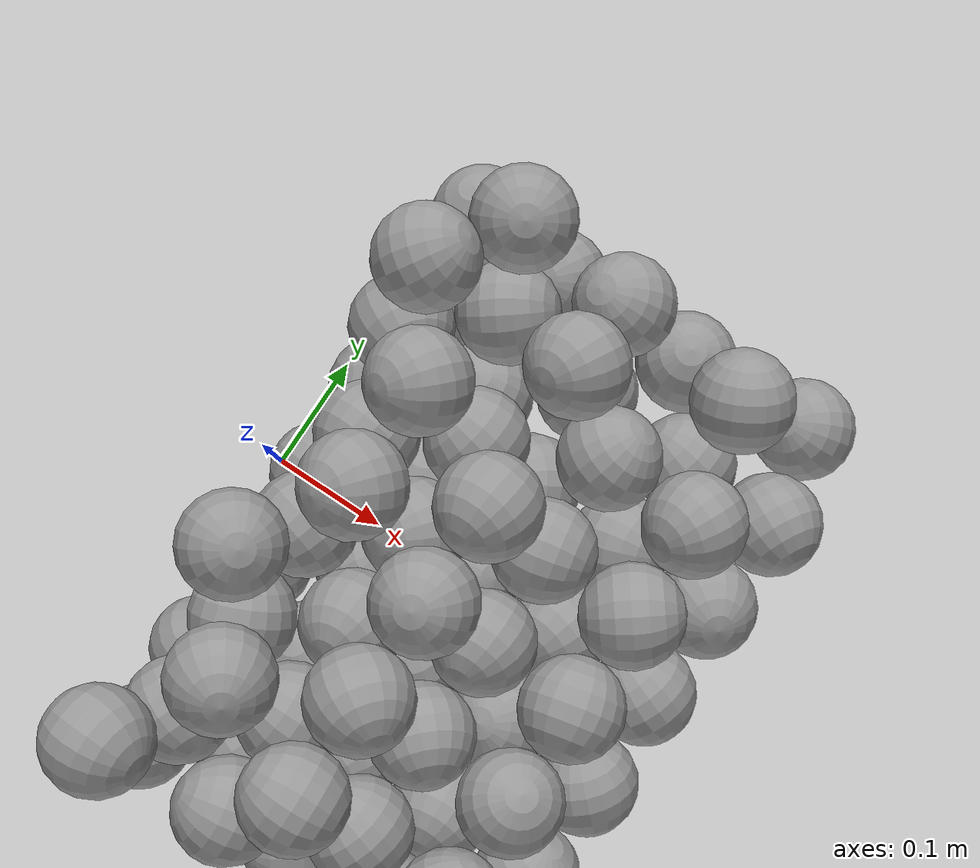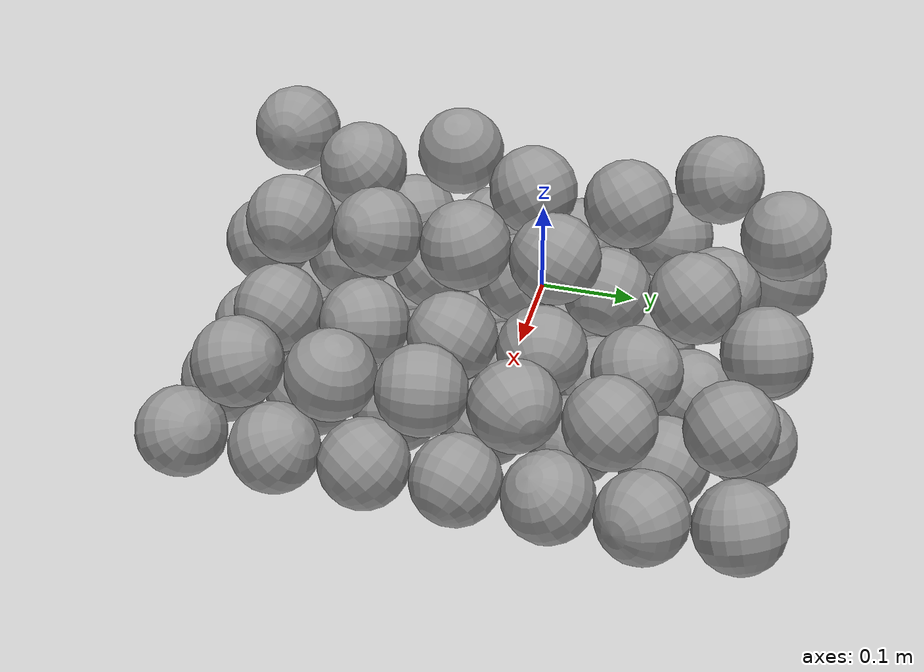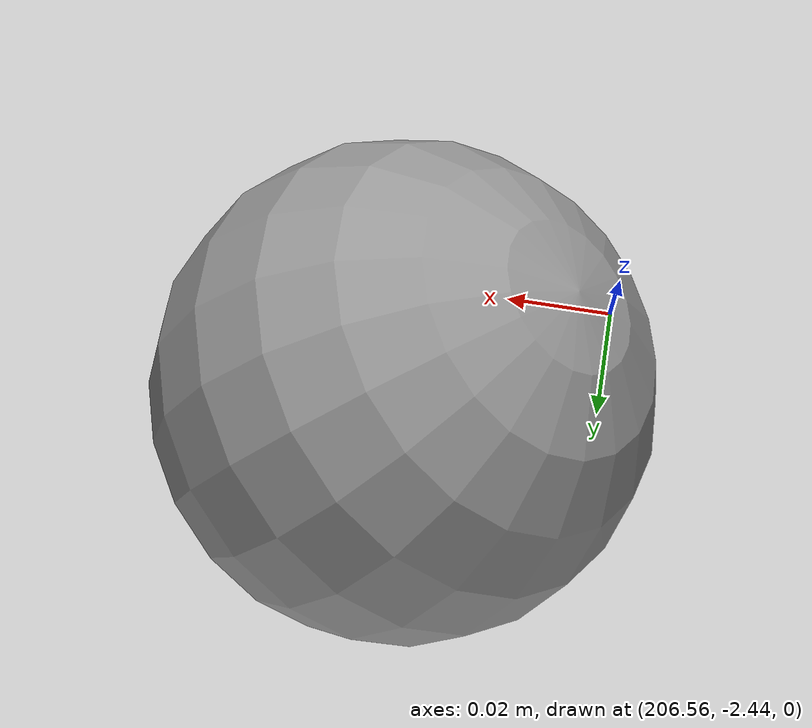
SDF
<sdf version="1.6">
 <world name="default">
  <light name="sun" type="directional">
   <pose>0 0 10 0 -0 0</pose>
   <diffuse>0.8 0.8 0.8 1</diffuse>
   <specular>0.2 0.2 0.2 1</specular>
   <attenuation>
    <range>1000</range>
    <constant>0.9</constant>
    <linear>0.01</linear>
    <quadratic>0.001</quadratic>
   </attenuation>
   <direction>-0.5 0.1 -0.9</direction>
  </light>
  <model name="ground_plane">
   <static>1</static>
   <link name="link">
    <collision name="collision">
     <geometry><plane><normal>0 0 1</normal><size>100 100</size></plane></geometry>
     <surface>
      <contact><collide_bitmask>65535</collide_bitmask></contact>
      <friction><ode><mu>100</mu><mu2>50</mu2></ode></friction>
     </surface>
    </collision>
    <visual name="visual">
     <cast_shadows>0</cast_shadows>
     <geometry><plane><normal>0 0 1</normal><size>100 100</size></plane></geometry>
     <material>
      <script><uri>file://media/materials/scripts/gazebo.material</uri><name>Gazebo/Grey</name></script>
     </material>
    </visual>
   </link>
  </model>
  <gravity>0 0 -9.8</gravity>
  <magnetic_field>6e-06 2.3e-05 -4.2e-05</magnetic_field>
  <atmosphere type="adiabatic"/>
  <physics name="default_physics" default="0" type="ode">
   <max_step_size>0.001</max_step_size>
   <real_time_factor>1</real_time_factor>
   <real_time_update_rate>1000</real_time_update_rate>
  </physics>
  <scene><ambient>0.4 0.4 0.4 1</ambient><background>0.7 0.7 0.7 1</background><shadows>1</shadows></scene>
  <spherical_coordinates>
   <surface_model>EARTH_WGS84</surface_model>
   <latitude_deg>0</latitude_deg>
   <longitude_deg>0</longitude_deg>
   <elevation>0</elevation>
   <heading_deg>0</heading_deg>
  </spherical_coordinates>
  <model name="unit_sphere_clone_2">
   <link name="link">
    <inertial>
     <mass>0.000642099</mass>
     <inertia>
      <ixx>4.77879e-07</ixx>
      <ixy>0</ixy>
      <ixz>0</ixz>
      <iyy>4.77879e-07</iyy>
      <iyz>0</iyz>
      <izz>4.77879e-07</izz>
     </inertia>
    </inertial>
    <visual name="visual">
     <geometry><sphere><radius>0.0431354</radius></sphere></geometry>
     <material>
      <script><name>Gazebo/Grey</name><uri>file://media/materials/scripts/gazebo.material</uri></script>
      <shader type="pixel"/>
      <ambient>0.3 0.3 0.3 1</ambient>
      <diffuse>0.7 0.7 0.7 1</diffuse>
      <specular>0.01 0.01 0.01 1</specular>
      <emissive>0 0 0 1</emissive>
     </material>
    </visual>
    <collision name="collision">
     <geometry><sphere><radius>0.043135</radius></sphere></geometry>
     <surface>
      <friction>
       <ode><mu>1</mu><mu2>1</mu2><fdir1>0 0 0</fdir1><slip1>0</slip1><slip2>0</slip2></ode>
       <torsional>
        <coefficient>1</coefficient>
        <patch_radius>0</patch_radius>
        <surface_radius>0</surface_radius>
        <use_patch_radius>1</use_patch_radius>
        <ode><slip>0</slip></ode>
       </torsional>
      </friction>
      <bounce><restitution_coefficient>0</restitution_coefficient><threshold>1e+06</threshold></bounce>
      <contact>
       <collide_without_contact>0</collide_without_contact>
       <collide_without_contact_bitmask>1</collide_without_contact_bitmask>
       <collide_bitmask>1</collide_bitmask>
       <ode>
        <soft_cfm>0</soft_cfm>
        <soft_erp>0.2</soft_erp>
        <kp>1e+13</kp>
        <kd>1</kd>
        <max_vel>0.01</max_vel>
        <min_depth>0</min_depth>
       </ode>
       <bullet>
        <split_impulse>1</split_impulse>
        <split_impulse_penetration_threshold>-0.01</split_impulse_penetration_threshold>
        <soft_cfm>0</soft_cfm>
        <soft_erp>0.2</soft_erp>
        <kp>1e+13</kp>
        <kd>1</kd>
       </bullet>
      </contact>
     </surface>
    </collision>
   </link>
   <static>0</static>
   <pose>0.116378 0.052367 0.043135 2.93694 0.319176 1.36025</pose>
  </model>
  <model name="unit_sphere_clone_10">
   <link name="link">
    <inertial>
     <mass>0.000642099</mass>
     <inertia>
      <ixx>4.77879e-07</ixx>
      <ixy>0</ixy>
      <ixz>0</ixz>
      <iyy>4.77879e-07</iyy>
      <iyz>0</iyz>
      <izz>4.77879e-07</izz>
     </inertia>
    </inertial>
    <visual name="visual">
     <geometry><sphere><radius>0.0431354</radius></sphere></geometry>
     <material>
      <script><name>Gazebo/Grey</name><uri>file://media/materials/scripts/gazebo.material</uri></script>
      <shader type="pixel"/>
      <ambient>0.3 0.3 0.3 1</ambient>
      <diffuse>0.7 0.7 0.7 1</diffuse>
      <specular>0.01 0.01 0.01 1</specular>
      <emissive>0 0 0 1</emissive>
     </material>
    </visual>
    <collision name="collision">
     <geometry><sphere><radius>0.043135</radius></sphere></geometry>
     <surface>
      <friction>
       <ode><mu>1</mu><mu2>1</mu2><fdir1>0 0 0</fdir1><slip1>0</slip1><slip2>0</slip2></ode>
       <torsional>
        <coefficient>1</coefficient>
        <patch_radius>0</patch_radius>
        <surface_radius>0</surface_radius>
        <use_patch_radius>1</use_patch_radius>
        <ode><slip>0</slip></ode>
       </torsional>
      </friction>
      <bounce><restitution_coefficient>0</restitution_coefficient><threshold>1e+06</threshold></bounce>
      <contact>
       <collide_without_contact>0</collide_without_contact>
       <collide_without_contact_bitmask>1</collide_without_contact_bitmask>
       <collide_bitmask>1</collide_bitmask>
       <ode>
        <soft_cfm>0</soft_cfm>
        <soft_erp>0.2</soft_erp>
        <kp>1e+13</kp>
        <kd>1</kd>
        <max_vel>0.01</max_vel>
        <min_depth>0</min_depth>
       </ode>
       <bullet>
        <split_impulse>1</split_impulse>
        <split_impulse_penetration_threshold>-0.01</split_impulse_penetration_threshold>
        <soft_cfm>0</soft_cfm>
        <soft_erp>0.2</soft_erp>
        <kp>1e+13</kp>
        <kd>1</kd>
       </bullet>
      </contact>
     </surface>
    </collision>
   </link>
   <static>0</static>
   <pose>0.040377 -0.249262 0.043127 -0.408895 -0.242678 -2.0554</pose>
  </model>
  <model name="unit_sphere_clone_2_clone">
   <link name="link">
    <inertial>
     <mass>0.000642099</mass>
     <inertia>
      <ixx>4.77879e-07</ixx>
      <ixy>0</ixy>
      <ixz>0</ixz>
      <iyy>4.77879e-07</iyy>
      <iyz>0</iyz>
      <izz>4.77879e-07</izz>
     </inertia>
    </inertial>
    <visual name="visual">
     <geometry><sphere><radius>0.0431354</radius></sphere></geometry>
     <material>
      <script><name>Gazebo/Grey</name><uri>file://media/materials/scripts/gazebo.material</uri></script>
      <shader type="pixel"/>
      <ambient>0.3 0.3 0.3 1</ambient>
      <diffuse>0.7 0.7 0.7 1</diffuse>
      <specular>0.01 0.01 0.01 1</specular>
      <emissive>0 0 0 1</emissive>
     </material>
    </visual>
    <collision name="collision">
     <geometry><sphere><radius>0.043135</radius></sphere></geometry>
     <surface>
      <friction>
       <ode><mu>1</mu><mu2>1</mu2><fdir1>0 0 0</fdir1><slip1>0</slip1><slip2>0</slip2></ode>
       <torsional>
        <coefficient>1</coefficient>
        <patch_radius>0</patch_radius>
        <surface_radius>0</surface_radius>
        <use_patch_radius>1</use_patch_radius>
        <ode><slip>0</slip></ode>
       </torsional>
      </friction>
      <bounce><restitution_coefficient>0</restitution_coefficient><threshold>1e+06</threshold></bounce>
      <contact>
       <collide_without_contact>0</collide_without_contact>
       <collide_without_contact_bitmask>1</collide_without_contact_bitmask>
       <collide_bitmask>1</collide_bitmask>
       <ode>
        <soft_cfm>0</soft_cfm>
        <soft_erp>0.2</soft_erp>
        <kp>1e+13</kp>
        <kd>1</kd>
        <max_vel>0.01</max_vel>
        <min_depth>0</min_depth>
       </ode>
       <bullet>
        <split_impulse>1</split_impulse>
        <split_impulse_penetration_threshold>-0.01</split_impulse_penetration_threshold>
        <soft_cfm>0</soft_cfm>
        <soft_erp>0.2</soft_erp>
        <kp>1e+13</kp>
        <kd>1</kd>
       </bullet>
      </contact>
     </surface>
    </collision>
   </link>
   <static>0</static>
   <pose>0.375758 0.175279 0.05281 -1.34273 0.461823 -1.95547</pose>
  </model>
  <model name="unit_sphere_clone_2_clone_2">
   <link name="link">
    <inertial>
     <mass>0.000642099</mass>
     <inertia>
      <ixx>4.77879e-07</ixx>
      <ixy>0</ixy>
      <ixz>0</ixz>
      <iyy>4.77879e-07</iyy>
      <iyz>0</iyz>
      <izz>4.77879e-07</izz>
     </inertia>
    </inertial>
    <visual name="visual">
     <geometry><sphere><radius>0.0431354</radius></sphere></geometry>
     <material>
      <script><name>Gazebo/Grey</name><uri>file://media/materials/scripts/gazebo.material</uri></script>
      <shader type="pixel"/>
      <ambient>0.3 0.3 0.3 1</ambient>
      <diffuse>0.7 0.7 0.7 1</diffuse>
      <specular>0.01 0.01 0.01 1</specular>
      <emissive>0 0 0 1</emissive>
     </material>
    </visual>
    <collision name="collision">
     <geometry><sphere><radius>0.043135</radius></sphere></geometry>
     <surface>
      <friction>
       <ode><mu>1</mu><mu2>1</mu2><fdir1>0 0 0</fdir1><slip1>0</slip1><slip2>0</slip2></ode>
       <torsional>
        <coefficient>1</coefficient>
        <patch_radius>0</patch_radius>
        <surface_radius>0</surface_radius>
        <use_patch_radius>1</use_patch_radius>
        <ode><slip>0</slip></ode>
       </torsional>
      </friction>
      <bounce><restitution_coefficient>0</restitution_coefficient><threshold>1e+06</threshold></bounce>
      <contact>
       <collide_without_contact>0</collide_without_contact>
       <collide_without_contact_bitmask>1</collide_without_contact_bitmask>
       <collide_bitmask>1</collide_bitmask>
       <ode>
        <soft_cfm>0</soft_cfm>
        <soft_erp>0.2</soft_erp>
        <kp>1e+13</kp>
        <kd>1</kd>
        <max_vel>0.01</max_vel>
        <min_depth>0</min_depth>
       </ode>
       <bullet>
        <split_impulse>1</split_impulse>
        <split_impulse_penetration_threshold>-0.01</split_impulse_penetration_threshold>
        <soft_cfm>0</soft_cfm>
        <soft_erp>0.2</soft_erp>
        <kp>1e+13</kp>
        <kd>1</kd>
       </bullet>
      </contact>
     </surface>
    </collision>
   </link>
   <static>0</static>
   <pose>0.041109 -0.076719 0.043134 -2.75724 -0.637083 -1.52655</pose>
  </model>
  <model name="unit_sphere_clone_2_clone_3">
   <link name="link">
    <inertial>
     <mass>0.000642099</mass>
     <inertia>
      <ixx>4.77879e-07</ixx>
      <ixy>0</ixy>
      <ixz>0</ixz>
      <iyy>4.77879e-07</iyy>
      <iyz>0</iyz>
      <izz>4.77879e-07</izz>
     </inertia>
    </inertial>
    <visual name="visual">
     <geometry><sphere><radius>0.0431354</radius></sphere></geometry>
     <material>
      <script><name>Gazebo/Grey</name><uri>file://media/materials/scripts/gazebo.material</uri></script>
      <shader type="pixel"/>
      <ambient>0.3 0.3 0.3 1</ambient>
      <diffuse>0.7 0.7 0.7 1</diffuse>
      <specular>0.01 0.01 0.01 1</specular>
      <emissive>0 0 0 1</emissive>
     </material>
    </visual>
    <collision name="collision">
     <geometry><sphere><radius>0.043135</radius></sphere></geometry>
     <surface>
      <friction>
       <ode><mu>1</mu><mu2>1</mu2><fdir1>0 0 0</fdir1><slip1>0</slip1><slip2>0</slip2></ode>
       <torsional>
        <coefficient>1</coefficient>
        <patch_radius>0</patch_radius>
        <surface_radius>0</surface_radius>
        <use_patch_radius>1</use_patch_radius>
        <ode><slip>0</slip></ode>
       </torsional>
      </friction>
      <bounce><restitution_coefficient>0</restitution_coefficient><threshold>1e+06</threshold></bounce>
      <contact>
       <collide_without_contact>0</collide_without_contact>
       <collide_without_contact_bitmask>1</collide_without_contact_bitmask>
       <collide_bitmask>1</collide_bitmask>
       <ode>
        <soft_cfm>0</soft_cfm>
        <soft_erp>0.2</soft_erp>
        <kp>1e+13</kp>
        <kd>1</kd>
        <max_vel>0.01</max_vel>
        <min_depth>0</min_depth>
       </ode>
       <bullet>
        <split_impulse>1</split_impulse>
        <split_impulse_penetration_threshold>-0.01</split_impulse_penetration_threshold>
        <soft_cfm>0</soft_cfm>
        <soft_erp>0.2</soft_erp>
        <kp>1e+13</kp>
        <kd>1</kd>
       </bullet>
      </contact>
     </surface>
    </collision>
   </link>
   <static>0</static>
   <pose>0.041477 0.00955 0.043135 -2.13247 0.784232 1.08708</pose>
  </model>
  <model name="unit_sphere_clone_2_clone_4">
   <link name="link">
    <inertial>
     <mass>0.000642099</mass>
     <inertia>
      <ixx>4.77879e-07</ixx>
      <ixy>0</ixy>
      <ixz>0</ixz>
      <iyy>4.77879e-07</iyy>
      <iyz>0</iyz>
      <izz>4.77879e-07</izz>
     </inertia>
    </inertial>
    <visual name="visual">
     <geometry><sphere><radius>0.0431354</radius></sphere></geometry>
     <material>
      <script><name>Gazebo/Grey</name><uri>file://media/materials/scripts/gazebo.material</uri></script>
      <shader type="pixel"/>
      <ambient>0.3 0.3 0.3 1</ambient>
      <diffuse>0.7 0.7 0.7 1</diffuse>
      <specular>0.01 0.01 0.01 1</specular>
      <emissive>0 0 0 1</emissive>
     </material>
    </visual>
    <collision name="collision">
     <geometry><sphere><radius>0.043135</radius></sphere></geometry>
     <surface>
      <friction>
       <ode><mu>1</mu><mu2>1</mu2><fdir1>0 0 0</fdir1><slip1>0</slip1><slip2>0</slip2></ode>
       <torsional>
        <coefficient>1</coefficient>
        <patch_radius>0</patch_radius>
        <surface_radius>0</surface_radius>
        <use_patch_radius>1</use_patch_radius>
        <ode><slip>0</slip></ode>
       </torsional>
      </friction>
      <bounce><restitution_coefficient>0</restitution_coefficient><threshold>1e+06</threshold></bounce>
      <contact>
       <collide_without_contact>0</collide_without_contact>
       <collide_without_contact_bitmask>1</collide_without_contact_bitmask>
       <collide_bitmask>1</collide_bitmask>
       <ode>
        <soft_cfm>0</soft_cfm>
        <soft_erp>0.2</soft_erp>
        <kp>1e+13</kp>
        <kd>1</kd>
        <max_vel>0.01</max_vel>
        <min_depth>0</min_depth>
       </ode>
       <bullet>
        <split_impulse>1</split_impulse>
        <split_impulse_penetration_threshold>-0.01</split_impulse_penetration_threshold>
        <soft_cfm>0</soft_cfm>
        <soft_erp>0.2</soft_erp>
        <kp>1e+13</kp>
        <kd>1</kd>
       </bullet>
      </contact>
     </surface>
    </collision>
   </link>
   <static>0</static>
   <pose>0.362847 -0.082969 0.046444 -0.88253 -0.573731 0.402038</pose>
  </model>
  <model name="unit_sphere_clone_4_clone_1_clone">
   <link name="link">
    <inertial>
     <mass>0.000642099</mass>
     <inertia>
      <ixx>4.77879e-07</ixx>
      <ixy>0</ixy>
      <ixz>0</ixz>
      <iyy>4.77879e-07</iyy>
      <iyz>0</iyz>
      <izz>4.77879e-07</izz>
     </inertia>
    </inertial>
    <visual name="visual">
     <geometry><sphere><radius>0.0431354</radius></sphere></geometry>
     <material>
      <script><name>Gazebo/Grey</name><uri>file://media/materials/scripts/gazebo.material</uri></script>
      <shader type="pixel"/>
      <ambient>0.3 0.3 0.3 1</ambient>
      <diffuse>0.7 0.7 0.7 1</diffuse>
      <specular>0.01 0.01 0.01 1</specular>
      <emissive>0 0 0 1</emissive>
     </material>
    </visual>
    <collision name="collision">
     <geometry><sphere><radius>0.043135</radius></sphere></geometry>
     <surface>
      <friction>
       <ode><mu>1</mu><mu2>1</mu2><fdir1>0 0 0</fdir1><slip1>0</slip1><slip2>0</slip2></ode>
       <torsional>
        <coefficient>1</coefficient>
        <patch_radius>0</patch_radius>
        <surface_radius>0</surface_radius>
        <use_patch_radius>1</use_patch_radius>
        <ode><slip>0</slip></ode>
       </torsional>
      </friction>
      <bounce><restitution_coefficient>0</restitution_coefficient><threshold>1e+06</threshold></bounce>
      <contact>
       <collide_without_contact>0</collide_without_contact>
       <collide_without_contact_bitmask>1</collide_without_contact_bitmask>
       <collide_bitmask>1</collide_bitmask>
       <ode>
        <soft_cfm>0</soft_cfm>
        <soft_erp>0.2</soft_erp>
        <kp>1e+13</kp>
        <kd>1</kd>
        <max_vel>0.01</max_vel>
        <min_depth>0</min_depth>
       </ode>
       <bullet>
        <split_impulse>1</split_impulse>
        <split_impulse_penetration_threshold>-0.01</split_impulse_penetration_threshold>
        <soft_cfm>0</soft_cfm>
        <soft_erp>0.2</soft_erp>
        <kp>1e+13</kp>
        <kd>1</kd>
       </bullet>
      </contact>
     </surface>
    </collision>
   </link>
   <static>0</static>
   <pose>0.363222 0.003305 0.04647 -2.60839 1.05018 -2.89248</pose>
  </model>
  <model name="unit_sphere_clone_4_clone_1_clone_0_clone">
   <link name="link">
    <inertial>
     <mass>0.000642099</mass>
     <inertia>
      <ixx>4.77879e-07</ixx>
      <ixy>0</ixy>
      <ixz>0</ixz>
      <iyy>4.77879e-07</iyy>
      <iyz>0</iyz>
      <izz>4.77879e-07</izz>
     </inertia>
    </inertial>
    <visual name="visual">
     <geometry><sphere><radius>0.0431354</radius></sphere></geometry>
     <material>
      <script><name>Gazebo/Grey</name><uri>file://media/materials/scripts/gazebo.material</uri></script>
      <shader type="pixel"/>
      <ambient>0.3 0.3 0.3 1</ambient>
      <diffuse>0.7 0.7 0.7 1</diffuse>
      <specular>0.01 0.01 0.01 1</specular>
      <emissive>0 0 0 1</emissive>
     </material>
    </visual>
    <collision name="collision">
     <geometry><sphere><radius>0.043135</radius></sphere></geometry>
     <surface>
      <friction>
       <ode><mu>1</mu><mu2>1</mu2><fdir1>0 0 0</fdir1><slip1>0</slip1><slip2>0</slip2></ode>
       <torsional>
        <coefficient>1</coefficient>
        <patch_radius>0</patch_radius>
        <surface_radius>0</surface_radius>
        <use_patch_radius>1</use_patch_radius>
        <ode><slip>0</slip></ode>
       </torsional>
      </friction>
      <bounce><restitution_coefficient>0</restitution_coefficient><threshold>1e+06</threshold></bounce>
      <contact>
       <collide_without_contact>0</collide_without_contact>
       <collide_without_contact_bitmask>1</collide_without_contact_bitmask>
       <collide_bitmask>1</collide_bitmask>
       <ode>
        <soft_cfm>0</soft_cfm>
        <soft_erp>0.2</soft_erp>
        <kp>1e+13</kp>
        <kd>1</kd>
        <max_vel>0.01</max_vel>
        <min_depth>0</min_depth>
       </ode>
       <bullet>
        <split_impulse>1</split_impulse>
        <split_impulse_penetration_threshold>-0.01</split_impulse_penetration_threshold>
        <soft_cfm>0</soft_cfm>
        <soft_erp>0.2</soft_erp>
        <kp>1e+13</kp>
        <kd>1</kd>
       </bullet>
      </contact>
     </surface>
    </collision>
   </link>
   <static>0</static>
   <pose>0.190531 -0.077357 0.043134 -0.426766 0.4755 1.58526</pose>
  </model>
  <model name="unit_sphere_clone_4_clone_1_clone_0_clone_0">
   <link name="link">
    <inertial>
     <mass>0.000642099</mass>
     <inertia>
      <ixx>4.77879e-07</ixx>
      <ixy>0</ixy>
      <ixz>0</ixz>
      <iyy>4.77879e-07</iyy>
      <iyz>0</iyz>
      <izz>4.77879e-07</izz>
     </inertia>
    </inertial>
    <visual name="visual">
     <geometry><sphere><radius>0.0431354</radius></sphere></geometry>
     <material>
      <script><name>Gazebo/Grey</name><uri>file://media/materials/scripts/gazebo.material</uri></script>
      <shader type="pixel"/>
      <ambient>0.3 0.3 0.3 1</ambient>
      <diffuse>0.7 0.7 0.7 1</diffuse>
      <specular>0.01 0.01 0.01 1</specular>
      <emissive>0 0 0 1</emissive>
     </material>
    </visual>
    <collision name="collision">
     <geometry><sphere><radius>0.043135</radius></sphere></geometry>
     <surface>
      <friction>
       <ode><mu>1</mu><mu2>1</mu2><fdir1>0 0 0</fdir1><slip1>0</slip1><slip2>0</slip2></ode>
       <torsional>
        <coefficient>1</coefficient>
        <patch_radius>0</patch_radius>
        <surface_radius>0</surface_radius>
        <use_patch_radius>1</use_patch_radius>
        <ode><slip>0</slip></ode>
       </torsional>
      </friction>
      <bounce><restitution_coefficient>0</restitution_coefficient><threshold>1e+06</threshold></bounce>
      <contact>
       <collide_without_contact>0</collide_without_contact>
       <collide_without_contact_bitmask>1</collide_without_contact_bitmask>
       <collide_bitmask>1</collide_bitmask>
       <ode>
        <soft_cfm>0</soft_cfm>
        <soft_erp>0.2</soft_erp>
        <kp>1e+13</kp>
        <kd>1</kd>
        <max_vel>0.01</max_vel>
        <min_depth>0</min_depth>
       </ode>
       <bullet>
        <split_impulse>1</split_impulse>
        <split_impulse_penetration_threshold>-0.01</split_impulse_penetration_threshold>
        <soft_cfm>0</soft_cfm>
        <soft_erp>0.2</soft_erp>
        <kp>1e+13</kp>
        <kd>1</kd>
       </bullet>
      </contact>
     </surface>
    </collision>
   </link>
   <static>0</static>
   <pose>0.277178 0.008545 0.043135 2.24902 0.729689 -2.89688</pose>
  </model>
  <model name="unit_sphere_clone_2_clone_2_clone_3_clone_clone_clone_clone">
   <link name="link">
    <inertial>
     <mass>0.000642099</mass>
     <inertia>
      <ixx>4.77879e-07</ixx>
      <ixy>0</ixy>
      <ixz>0</ixz>
      <iyy>4.77879e-07</iyy>
      <iyz>0</iyz>
      <izz>4.77879e-07</izz>
     </inertia>
    </inertial>
    <visual name="visual">
     <geometry><sphere><radius>0.0431354</radius></sphere></geometry>
     <material>
      <script><name>Gazebo/Grey</name><uri>file://media/materials/scripts/gazebo.material</uri></script>
      <shader type="pixel"/>
      <ambient>0.3 0.3 0.3 1</ambient>
      <diffuse>0.7 0.7 0.7 1</diffuse>
      <specular>0.01 0.01 0.01 1</specular>
      <emissive>0 0 0 1</emissive>
     </material>
    </visual>
    <collision name="collision">
     <geometry><sphere><radius>0.043135</radius></sphere></geometry>
     <surface>
      <friction>
       <ode><mu>1</mu><mu2>1</mu2><fdir1>0 0 0</fdir1><slip1>0</slip1><slip2>0</slip2></ode>
       <torsional>
        <coefficient>1</coefficient>
        <patch_radius>0</patch_radius>
        <surface_radius>0</surface_radius>
        <use_patch_radius>1</use_patch_radius>
        <ode><slip>0</slip></ode>
       </torsional>
      </friction>
      <bounce><restitution_coefficient>0</restitution_coefficient><threshold>1e+06</threshold></bounce>
      <contact>
       <collide_without_contact>0</collide_without_contact>
       <collide_without_contact_bitmask>1</collide_without_contact_bitmask>
       <collide_bitmask>1</collide_bitmask>
       <ode>
        <soft_cfm>0</soft_cfm>
        <soft_erp>0.2</soft_erp>
        <kp>1e+13</kp>
        <kd>1</kd>
        <max_vel>0.01</max_vel>
        <min_depth>0</min_depth>
       </ode>
       <bullet>
        <split_impulse>1</split_impulse>
        <split_impulse_penetration_threshold>-0.01</split_impulse_penetration_threshold>
        <soft_cfm>0</soft_cfm>
        <soft_erp>0.2</soft_erp>
        <kp>1e+13</kp>
        <kd>1</kd>
       </bullet>
      </contact>
     </surface>
    </collision>
   </link>
   <static>0</static>
   <pose>0.04074 -0.162992 0.043135 -2.35775 0.164103 2.86462</pose>
  </model>
  <model name="unit_sphere_clone_2_clone_2_clone_3_clone_clone_clone_0_clone_clone">
   <link name="link">
    <inertial>
     <mass>0.000642099</mass>
     <inertia>
      <ixx>4.77879e-07</ixx>
      <ixy>0</ixy>
      <ixz>0</ixz>
      <iyy>4.77879e-07</iyy>
      <iyz>0</iyz>
      <izz>4.77879e-07</izz>
     </inertia>
    </inertial>
    <visual name="visual">
     <geometry><sphere><radius>0.0431354</radius></sphere></geometry>
     <material>
      <script><name>Gazebo/Grey</name><uri>file://media/materials/scripts/gazebo.material</uri></script>
      <shader type="pixel"/>
      <ambient>0.3 0.3 0.3 1</ambient>
      <diffuse>0.7 0.7 0.7 1</diffuse>
      <specular>0.01 0.01 0.01 1</specular>
      <emissive>0 0 0 1</emissive>
     </material>
    </visual>
    <collision name="collision">
     <geometry><sphere><radius>0.043135</radius></sphere></geometry>
     <surface>
      <friction>
       <ode><mu>1</mu><mu2>1</mu2><fdir1>0 0 0</fdir1><slip1>0</slip1><slip2>0</slip2></ode>
       <torsional>
        <coefficient>1</coefficient>
        <patch_radius>0</patch_radius>
        <surface_radius>0</surface_radius>
        <use_patch_radius>1</use_patch_radius>
        <ode><slip>0</slip></ode>
       </torsional>
      </friction>
      <bounce><restitution_coefficient>0</restitution_coefficient><threshold>1e+06</threshold></bounce>
      <contact>
       <collide_without_contact>0</collide_without_contact>
       <collide_without_contact_bitmask>1</collide_without_contact_bitmask>
       <collide_bitmask>1</collide_bitmask>
       <ode>
        <soft_cfm>0</soft_cfm>
        <soft_erp>0.2</soft_erp>
        <kp>1e+13</kp>
        <kd>1</kd>
        <max_vel>0.01</max_vel>
        <min_depth>0</min_depth>
       </ode>
       <bullet>
        <split_impulse>1</split_impulse>
        <split_impulse_penetration_threshold>-0.01</split_impulse_penetration_threshold>
        <soft_cfm>0</soft_cfm>
        <soft_erp>0.2</soft_erp>
        <kp>1e+13</kp>
        <kd>1</kd>
       </bullet>
      </contact>
     </surface>
    </collision>
   </link>
   <static>0</static>
   <pose>206.595 -2.40669 0.043135 -0.243882 -0.685972 0.78433</pose>
  </model>
  <model name="unit_sphere_clone_2_clone_2_clone_3_clone_clone_clone_0_clone_clone_clone">
   <link name="link">
    <inertial>
     <mass>0.000642099</mass>
     <inertia>
      <ixx>4.77879e-07</ixx>
      <ixy>0</ixy>
      <ixz>0</ixz>
      <iyy>4.77879e-07</iyy>
      <iyz>0</iyz>
      <izz>4.77879e-07</izz>
     </inertia>
    </inertial>
    <visual name="visual">
     <geometry><sphere><radius>0.0431354</radius></sphere></geometry>
     <material>
      <script><name>Gazebo/Grey</name><uri>file://media/materials/scripts/gazebo.material</uri></script>
      <shader type="pixel"/>
      <ambient>0.3 0.3 0.3 1</ambient>
      <diffuse>0.7 0.7 0.7 1</diffuse>
      <specular>0.01 0.01 0.01 1</specular>
      <emissive>0 0 0 1</emissive>
     </material>
    </visual>
    <collision name="collision">
     <geometry><sphere><radius>0.043135</radius></sphere></geometry>
     <surface>
      <friction>
       <ode><mu>1</mu><mu2>1</mu2><fdir1>0 0 0</fdir1><slip1>0</slip1><slip2>0</slip2></ode>
       <torsional>
        <coefficient>1</coefficient>
        <patch_radius>0</patch_radius>
        <surface_radius>0</surface_radius>
        <use_patch_radius>1</use_patch_radius>
        <ode><slip>0</slip></ode>
       </torsional>
      </friction>
      <bounce><restitution_coefficient>0</restitution_coefficient><threshold>1e+06</threshold></bounce>
      <contact>
       <collide_without_contact>0</collide_without_contact>
       <collide_without_contact_bitmask>1</collide_without_contact_bitmask>
       <collide_bitmask>1</collide_bitmask>
       <ode>
        <soft_cfm>0</soft_cfm>
        <soft_erp>0.2</soft_erp>
        <kp>1e+13</kp>
        <kd>1</kd>
        <max_vel>0.01</max_vel>
        <min_depth>0</min_depth>
       </ode>
       <bullet>
        <split_impulse>1</split_impulse>
        <split_impulse_penetration_threshold>-0.01</split_impulse_penetration_threshold>
        <soft_cfm>0</soft_cfm>
        <soft_erp>0.2</soft_erp>
        <kp>1e+13</kp>
        <kd>1</kd>
       </bullet>
      </contact>
     </surface>
    </collision>
   </link>
   <static>0</static>
   <pose>0.115634 -0.120174 0.043135 3.12467 -0.26362 -0.311444</pose>
  </model>
  <model name="unit_sphere_clone_2_clone_2_clone_3_clone_clone_clone_0_clone_clone_clone_clone">
   <link name="link">
    <inertial>
     <mass>0.000642099</mass>
     <inertia>
      <ixx>4.77879e-07</ixx>
      <ixy>0</ixy>
      <ixz>0</ixz>
      <iyy>4.77879e-07</iyy>
      <iyz>0</iyz>
      <izz>4.77879e-07</izz>
     </inertia>
    </inertial>
    <visual name="visual">
     <geometry><sphere><radius>0.0431354</radius></sphere></geometry>
     <material>
      <script><name>Gazebo/Grey</name><uri>file://media/materials/scripts/gazebo.material</uri></script>
      <shader type="pixel"/>
      <ambient>0.3 0.3 0.3 1</ambient>
      <diffuse>0.7 0.7 0.7 1</diffuse>
      <specular>0.01 0.01 0.01 1</specular>
      <emissive>0 0 0 1</emissive>
     </material>
    </visual>
    <collision name="collision">
     <geometry><sphere><radius>0.043135</radius></sphere></geometry>
     <surface>
      <friction>
       <ode><mu>1</mu><mu2>1</mu2><fdir1>0 0 0</fdir1><slip1>0</slip1><slip2>0</slip2></ode>
       <torsional>
        <coefficient>1</coefficient>
        <patch_radius>0</patch_radius>
        <surface_radius>0</surface_radius>
        <use_patch_radius>1</use_patch_radius>
        <ode><slip>0</slip></ode>
       </torsional>
      </friction>
      <bounce><restitution_coefficient>0</restitution_coefficient><threshold>1e+06</threshold></bounce>
      <contact>
       <collide_without_contact>0</collide_without_contact>
       <collide_without_contact_bitmask>1</collide_without_contact_bitmask>
       <collide_bitmask>1</collide_bitmask>
       <ode>
        <soft_cfm>0</soft_cfm>
        <soft_erp>0.2</soft_erp>
        <kp>1e+13</kp>
        <kd>1</kd>
        <max_vel>0.01</max_vel>
        <min_depth>0</min_depth>
       </ode>
       <bullet>
        <split_impulse>1</split_impulse>
        <split_impulse_penetration_threshold>-0.01</split_impulse_penetration_threshold>
        <soft_cfm>0</soft_cfm>
        <soft_erp>0.2</soft_erp>
        <kp>1e+13</kp>
        <kd>1</kd>
       </bullet>
      </contact>
     </surface>
    </collision>
   </link>
   <static>0</static>
   <pose>0.361612 -0.261033 0.045988 -2.29451 -0.19091 2.71243</pose>
  </model>
  <model name="unit_sphere_clone_2_clone_2_clone_3_clone_clone_clone_0_clone_clone_clone_1">
   <link name="link">
    <inertial>
     <mass>0.000642099</mass>
     <inertia>
      <ixx>4.77879e-07</ixx>
      <ixy>0</ixy>
      <ixz>0</ixz>
      <iyy>4.77879e-07</iyy>
      <iyz>0</iyz>
      <izz>4.77879e-07</izz>
     </inertia>
    </inertial>
    <visual name="visual">
     <geometry><sphere><radius>0.0431354</radius></sphere></geometry>
     <material>
      <script><name>Gazebo/Grey</name><uri>file://media/materials/scripts/gazebo.material</uri></script>
      <shader type="pixel"/>
      <ambient>0.3 0.3 0.3 1</ambient>
      <diffuse>0.7 0.7 0.7 1</diffuse>
      <specular>0.01 0.01 0.01 1</specular>
      <emissive>0 0 0 1</emissive>
     </material>
    </visual>
    <collision name="collision">
     <geometry><sphere><radius>0.043135</radius></sphere></geometry>
     <surface>
      <friction>
       <ode><mu>1</mu><mu2>1</mu2><fdir1>0 0 0</fdir1><slip1>0</slip1><slip2>0</slip2></ode>
       <torsional>
        <coefficient>1</coefficient>
        <patch_radius>0</patch_radius>
        <surface_radius>0</surface_radius>
        <use_patch_radius>1</use_patch_radius>
        <ode><slip>0</slip></ode>
       </torsional>
      </friction>
      <bounce><restitution_coefficient>0</restitution_coefficient><threshold>1e+06</threshold></bounce>
      <contact>
       <collide_without_contact>0</collide_without_contact>
       <collide_without_contact_bitmask>1</collide_without_contact_bitmask>
       <collide_bitmask>1</collide_bitmask>
       <ode>
        <soft_cfm>0</soft_cfm>
        <soft_erp>0.2</soft_erp>
        <kp>1e+13</kp>
        <kd>1</kd>
        <max_vel>0.01</max_vel>
        <min_depth>0</min_depth>
       </ode>
       <bullet>
        <split_impulse>1</split_impulse>
        <split_impulse_penetration_threshold>-0.01</split_impulse_penetration_threshold>
        <soft_cfm>0</soft_cfm>
        <soft_erp>0.2</soft_erp>
        <kp>1e+13</kp>
        <kd>1</kd>
       </bullet>
      </contact>
     </surface>
    </collision>
   </link>
   <static>0</static>
   <pose>0.190163 -0.163627 0.043135 -2.80884 -0.748861 0.920118</pose>
  </model>
  <model name="unit_sphere_clone_2_clone_2_clone_3_clone_clone_clone_0_clone_clone_clone_5">
   <link name="link">
    <inertial>
     <mass>0.000642099</mass>
     <inertia>
      <ixx>4.77879e-07</ixx>
      <ixy>0</ixy>
      <ixz>0</ixz>
      <iyy>4.77879e-07</iyy>
      <iyz>0</iyz>
      <izz>4.77879e-07</izz>
     </inertia>
    </inertial>
    <visual name="visual">
     <geometry><sphere><radius>0.0431354</radius></sphere></geometry>
     <material>
      <script><name>Gazebo/Grey</name><uri>file://media/materials/scripts/gazebo.material</uri></script>
      <shader type="pixel"/>
      <ambient>0.3 0.3 0.3 1</ambient>
      <diffuse>0.7 0.7 0.7 1</diffuse>
      <specular>0.01 0.01 0.01 1</specular>
      <emissive>0 0 0 1</emissive>
     </material>
    </visual>
    <collision name="collision">
     <geometry><sphere><radius>0.043135</radius></sphere></geometry>
     <surface>
      <friction>
       <ode><mu>1</mu><mu2>1</mu2><fdir1>0 0 0</fdir1><slip1>0</slip1><slip2>0</slip2></ode>
       <torsional>
        <coefficient>1</coefficient>
        <patch_radius>0</patch_radius>
        <surface_radius>0</surface_radius>
        <use_patch_radius>1</use_patch_radius>
        <ode><slip>0</slip></ode>
       </torsional>
      </friction>
      <bounce><restitution_coefficient>0</restitution_coefficient><threshold>1e+06</threshold></bounce>
      <contact>
       <collide_without_contact>0</collide_without_contact>
       <collide_without_contact_bitmask>1</collide_without_contact_bitmask>
       <collide_bitmask>1</collide_bitmask>
       <ode>
        <soft_cfm>0</soft_cfm>
        <soft_erp>0.2</soft_erp>
        <kp>1e+13</kp>
        <kd>1</kd>
        <max_vel>0.01</max_vel>
        <min_depth>0</min_depth>
       </ode>
       <bullet>
        <split_impulse>1</split_impulse>
        <split_impulse_penetration_threshold>-0.01</split_impulse_penetration_threshold>
        <soft_cfm>0</soft_cfm>
        <soft_erp>0.2</soft_erp>
        <kp>1e+13</kp>
        <kd>1</kd>
       </bullet>
      </contact>
     </surface>
    </collision>
   </link>
   <static>0</static>
   <pose>0.276431 -0.163993 0.043137 -2.18756 -0.564432 0.415618</pose>
  </model>
  <model name="unit_sphere_clone_2_clone_2_clone_3_clone_clone_clone_0_clone_clone_clone_6">
   <link name="link">
    <inertial>
     <mass>0.000642099</mass>
     <inertia>
      <ixx>4.77879e-07</ixx>
      <ixy>0</ixy>
      <ixz>0</ixz>
      <iyy>4.77879e-07</iyy>
      <iyz>0</iyz>
      <izz>4.77879e-07</izz>
     </inertia>
    </inertial>
    <visual name="visual">
     <geometry><sphere><radius>0.0431354</radius></sphere></geometry>
     <material>
      <script><name>Gazebo/Grey</name><uri>file://media/materials/scripts/gazebo.material</uri></script>
      <shader type="pixel"/>
      <ambient>0.3 0.3 0.3 1</ambient>
      <diffuse>0.7 0.7 0.7 1</diffuse>
      <specular>0.01 0.01 0.01 1</specular>
      <emissive>0 0 0 1</emissive>
     </material>
    </visual>
    <collision name="collision">
     <geometry><sphere><radius>0.043135</radius></sphere></geometry>
     <surface>
      <friction>
       <ode><mu>1</mu><mu2>1</mu2><fdir1>0 0 0</fdir1><slip1>0</slip1><slip2>0</slip2></ode>
       <torsional>
        <coefficient>1</coefficient>
        <patch_radius>0</patch_radius>
        <surface_radius>0</surface_radius>
        <use_patch_radius>1</use_patch_radius>
        <ode><slip>0</slip></ode>
       </torsional>
      </friction>
      <bounce><restitution_coefficient>0</restitution_coefficient><threshold>1e+06</threshold></bounce>
      <contact>
       <collide_without_contact>0</collide_without_contact>
       <collide_without_contact_bitmask>1</collide_without_contact_bitmask>
       <collide_bitmask>1</collide_bitmask>
       <ode>
        <soft_cfm>0</soft_cfm>
        <soft_erp>0.2</soft_erp>
        <kp>1e+13</kp>
        <kd>1</kd>
        <max_vel>0.01</max_vel>
        <min_depth>0</min_depth>
       </ode>
       <bullet>
        <split_impulse>1</split_impulse>
        <split_impulse_penetration_threshold>-0.01</split_impulse_penetration_threshold>
        <soft_cfm>0</soft_cfm>
        <soft_erp>0.2</soft_erp>
        <kp>1e+13</kp>
        <kd>1</kd>
       </bullet>
      </contact>
     </surface>
    </collision>
   </link>
   <static>0</static>
   <pose>0.276066 -0.250266 0.043133 1.19181 -0.774067 -2.47513</pose>
  </model>
  <model name="unit_sphere_clone_2_clone_2_clone_3_clone_clone_clone_0_clone_clone_clone_0_clone_1_clone_0_clone_1_clone_1">
   <link name="link">
    <inertial>
     <mass>0.000642099</mass>
     <inertia>
      <ixx>4.77879e-07</ixx>
      <ixy>0</ixy>
      <ixz>0</ixz>
      <iyy>4.77879e-07</iyy>
      <iyz>0</iyz>
      <izz>4.77879e-07</izz>
     </inertia>
    </inertial>
    <visual name="visual">
     <geometry><sphere><radius>0.0431354</radius></sphere></geometry>
     <material>
      <script><name>Gazebo/Grey</name><uri>file://media/materials/scripts/gazebo.material</uri></script>
      <shader type="pixel"/>
      <ambient>0.3 0.3 0.3 1</ambient>
      <diffuse>0.7 0.7 0.7 1</diffuse>
      <specular>0.01 0.01 0.01 1</specular>
      <emissive>0 0 0 1</emissive>
     </material>
    </visual>
    <collision name="collision">
     <geometry><sphere><radius>0.043135</radius></sphere></geometry>
     <surface>
      <friction>
       <ode><mu>1</mu><mu2>1</mu2><fdir1>0 0 0</fdir1><slip1>0</slip1><slip2>0</slip2></ode>
       <torsional>
        <coefficient>1</coefficient>
        <patch_radius>0</patch_radius>
        <surface_radius>0</surface_radius>
        <use_patch_radius>1</use_patch_radius>
        <ode><slip>0</slip></ode>
       </torsional>
      </friction>
      <bounce><restitution_coefficient>0</restitution_coefficient><threshold>1e+06</threshold></bounce>
      <contact>
       <collide_without_contact>0</collide_without_contact>
       <collide_without_contact_bitmask>1</collide_without_contact_bitmask>
       <collide_bitmask>1</collide_bitmask>
       <ode>
        <soft_cfm>0</soft_cfm>
        <soft_erp>0.2</soft_erp>
        <kp>1e+13</kp>
        <kd>1</kd>
        <max_vel>0.01</max_vel>
        <min_depth>0</min_depth>
       </ode>
       <bullet>
        <split_impulse>1</split_impulse>
        <split_impulse_penetration_threshold>-0.01</split_impulse_penetration_threshold>
        <soft_cfm>0</soft_cfm>
        <soft_erp>0.2</soft_erp>
        <kp>1e+13</kp>
        <kd>1</kd>
       </bullet>
      </contact>
     </surface>
    </collision>
   </link>
   <static>0</static>
   <pose>0.2768 -0.077724 0.043136 0.19922 -0.357076 0.268702</pose>
  </model>
  <model name="unit_sphere_clone_4_clone_1_clone_1">
   <link name="link">
    <inertial>
     <mass>0.000642099</mass>
     <inertia>
      <ixx>4.77879e-07</ixx>
      <ixy>0</ixy>
      <ixz>0</ixz>
      <iyy>4.77879e-07</iyy>
      <iyz>0</iyz>
      <izz>4.77879e-07</izz>
     </inertia>
    </inertial>
    <visual name="visual">
     <geometry><sphere><radius>0.0431354</radius></sphere></geometry>
     <material>
      <script><name>Gazebo/Grey</name><uri>file://media/materials/scripts/gazebo.material</uri></script>
      <shader type="pixel"/>
      <ambient>0.3 0.3 0.3 1</ambient>
      <diffuse>0.7 0.7 0.7 1</diffuse>
      <specular>0.01 0.01 0.01 1</specular>
      <emissive>0 0 0 1</emissive>
     </material>
    </visual>
    <collision name="collision">
     <geometry><sphere><radius>0.043135</radius></sphere></geometry>
     <surface>
      <friction>
       <ode><mu>1</mu><mu2>1</mu2><fdir1>0 0 0</fdir1><slip1>0</slip1><slip2>0</slip2></ode>
       <torsional>
        <coefficient>1</coefficient>
        <patch_radius>0</patch_radius>
        <surface_radius>0</surface_radius>
        <use_patch_radius>1</use_patch_radius>
        <ode><slip>0</slip></ode>
       </torsional>
      </friction>
      <bounce><restitution_coefficient>0</restitution_coefficient><threshold>1e+06</threshold></bounce>
      <contact>
       <collide_without_contact>0</collide_without_contact>
       <collide_without_contact_bitmask>1</collide_without_contact_bitmask>
       <collide_bitmask>1</collide_bitmask>
       <ode>
        <soft_cfm>0</soft_cfm>
        <soft_erp>0.2</soft_erp>
        <kp>1e+13</kp>
        <kd>1</kd>
        <max_vel>0.01</max_vel>
        <min_depth>0</min_depth>
       </ode>
       <bullet>
        <split_impulse>1</split_impulse>
        <split_impulse_penetration_threshold>-0.01</split_impulse_penetration_threshold>
        <soft_cfm>0</soft_cfm>
        <soft_erp>0.2</soft_erp>
        <kp>1e+13</kp>
        <kd>1</kd>
       </bullet>
      </contact>
     </surface>
    </collision>
   </link>
   <static>0</static>
   <pose>0.31989 -0.039659 0.107454 -1.27759 1.33711 -2.64391</pose>
  </model>
  <model name="unit_sphere_clone_4_clone_1_clone_3_clone_2">
   <link name="link">
    <inertial>
     <mass>0.000642099</mass>
     <inertia>
      <ixx>4.77879e-07</ixx>
      <ixy>0</ixy>
      <ixz>0</ixz>
      <iyy>4.77879e-07</iyy>
      <iyz>0</iyz>
      <izz>4.77879e-07</izz>
     </inertia>
    </inertial>
    <visual name="visual">
     <geometry><sphere><radius>0.0431354</radius></sphere></geometry>
     <material>
      <script><name>Gazebo/Grey</name><uri>file://media/materials/scripts/gazebo.material</uri></script>
      <shader type="pixel"/>
      <ambient>0.3 0.3 0.3 1</ambient>
      <diffuse>0.7 0.7 0.7 1</diffuse>
      <specular>0.01 0.01 0.01 1</specular>
      <emissive>0 0 0 1</emissive>
     </material>
    </visual>
    <collision name="collision">
     <geometry><sphere><radius>0.043135</radius></sphere></geometry>
     <surface>
      <friction>
       <ode><mu>1</mu><mu2>1</mu2><fdir1>0 0 0</fdir1><slip1>0</slip1><slip2>0</slip2></ode>
       <torsional>
        <coefficient>1</coefficient>
        <patch_radius>0</patch_radius>
        <surface_radius>0</surface_radius>
        <use_patch_radius>1</use_patch_radius>
        <ode><slip>0</slip></ode>
       </torsional>
      </friction>
      <bounce><restitution_coefficient>0</restitution_coefficient><threshold>1e+06</threshold></bounce>
      <contact>
       <collide_without_contact>0</collide_without_contact>
       <collide_without_contact_bitmask>1</collide_without_contact_bitmask>
       <collide_bitmask>1</collide_bitmask>
       <ode>
        <soft_cfm>0</soft_cfm>
        <soft_erp>0.2</soft_erp>
        <kp>1e+13</kp>
        <kd>1</kd>
        <max_vel>0.01</max_vel>
        <min_depth>0</min_depth>
       </ode>
       <bullet>
        <split_impulse>1</split_impulse>
        <split_impulse_penetration_threshold>-0.01</split_impulse_penetration_threshold>
        <soft_cfm>0</soft_cfm>
        <soft_erp>0.2</soft_erp>
        <kp>1e+13</kp>
        <kd>1</kd>
       </bullet>
      </contact>
     </surface>
    </collision>
   </link>
   <static>0</static>
   <pose>0.36724 0.089444 0.049002 -0.529049 0.201941 -1.90392</pose>
  </model>
  <model name="unit_sphere_clone_4_clone_1_clone_3_clone_3">
   <link name="link">
    <inertial>
     <mass>0.000642099</mass>
     <inertia>
      <ixx>4.77879e-07</ixx>
      <ixy>0</ixy>
      <ixz>0</ixz>
      <iyy>4.77879e-07</iyy>
      <iyz>0</iyz>
      <izz>4.77879e-07</izz>
     </inertia>
    </inertial>
    <visual name="visual">
     <geometry><sphere><radius>0.0431354</radius></sphere></geometry>
     <material>
      <script><name>Gazebo/Grey</name><uri>file://media/materials/scripts/gazebo.material</uri></script>
      <shader type="pixel"/>
      <ambient>0.3 0.3 0.3 1</ambient>
      <diffuse>0.7 0.7 0.7 1</diffuse>
      <specular>0.01 0.01 0.01 1</specular>
      <emissive>0 0 0 1</emissive>
     </material>
    </visual>
    <collision name="collision">
     <geometry><sphere><radius>0.043135</radius></sphere></geometry>
     <surface>
      <friction>
       <ode><mu>1</mu><mu2>1</mu2><fdir1>0 0 0</fdir1><slip1>0</slip1><slip2>0</slip2></ode>
       <torsional>
        <coefficient>1</coefficient>
        <patch_radius>0</patch_radius>
        <surface_radius>0</surface_radius>
        <use_patch_radius>1</use_patch_radius>
        <ode><slip>0</slip></ode>
       </torsional>
      </friction>
      <bounce><restitution_coefficient>0</restitution_coefficient><threshold>1e+06</threshold></bounce>
      <contact>
       <collide_without_contact>0</collide_without_contact>
       <collide_without_contact_bitmask>1</collide_without_contact_bitmask>
       <collide_bitmask>1</collide_bitmask>
       <ode>
        <soft_cfm>0</soft_cfm>
        <soft_erp>0.2</soft_erp>
        <kp>1e+13</kp>
        <kd>1</kd>
        <max_vel>0.01</max_vel>
        <min_depth>0</min_depth>
       </ode>
       <bullet>
        <split_impulse>1</split_impulse>
        <split_impulse_penetration_threshold>-0.01</split_impulse_penetration_threshold>
        <soft_cfm>0</soft_cfm>
        <soft_erp>0.2</soft_erp>
        <kp>1e+13</kp>
        <kd>1</kd>
       </bullet>
      </contact>
     </surface>
    </collision>
   </link>
   <static>0</static>
   <pose>0.189797 -0.249892 0.043135 2.21495 0.205139 2.55789</pose>
  </model>
  <model name="unit_sphere_clone_4_clone_1_clone_3_clone_clone">
   <link name="link">
    <inertial>
     <mass>0.000642099</mass>
     <inertia>
      <ixx>4.77879e-07</ixx>
      <ixy>0</ixy>
      <ixz>0</ixz>
      <iyy>4.77879e-07</iyy>
      <iyz>0</iyz>
      <izz>4.77879e-07</izz>
     </inertia>
    </inertial>
    <visual name="visual">
     <geometry><sphere><radius>0.0431354</radius></sphere></geometry>
     <material>
      <script><name>Gazebo/Grey</name><uri>file://media/materials/scripts/gazebo.material</uri></script>
      <shader type="pixel"/>
      <ambient>0.3 0.3 0.3 1</ambient>
      <diffuse>0.7 0.7 0.7 1</diffuse>
      <specular>0.01 0.01 0.01 1</specular>
      <emissive>0 0 0 1</emissive>
     </material>
    </visual>
    <collision name="collision">
     <geometry><sphere><radius>0.043135</radius></sphere></geometry>
     <surface>
      <friction>
       <ode><mu>1</mu><mu2>1</mu2><fdir1>0 0 0</fdir1><slip1>0</slip1><slip2>0</slip2></ode>
       <torsional>
        <coefficient>1</coefficient>
        <patch_radius>0</patch_radius>
        <surface_radius>0</surface_radius>
        <use_patch_radius>1</use_patch_radius>
        <ode><slip>0</slip></ode>
       </torsional>
      </friction>
      <bounce><restitution_coefficient>0</restitution_coefficient><threshold>1e+06</threshold></bounce>
      <contact>
       <collide_without_contact>0</collide_without_contact>
       <collide_without_contact_bitmask>1</collide_without_contact_bitmask>
       <collide_bitmask>1</collide_bitmask>
       <ode>
        <soft_cfm>0</soft_cfm>
        <soft_erp>0.2</soft_erp>
        <kp>1e+13</kp>
        <kd>1</kd>
        <max_vel>0.01</max_vel>
        <min_depth>0</min_depth>
       </ode>
       <bullet>
        <split_impulse>1</split_impulse>
        <split_impulse_penetration_threshold>-0.01</split_impulse_penetration_threshold>
        <soft_cfm>0</soft_cfm>
        <soft_erp>0.2</soft_erp>
        <kp>1e+13</kp>
        <kd>1</kd>
       </bullet>
      </contact>
     </surface>
    </collision>
   </link>
   <static>0</static>
   <pose>0.319542 -0.125934 0.107446 0.150017 0.268294 1.78553</pose>
  </model>
  <model name="unit_sphere_clone_4_clone_1_clone_3_clone_1_clone_0">
   <link name="link">
    <inertial>
     <mass>0.000642099</mass>
     <inertia>
      <ixx>4.77879e-07</ixx>
      <ixy>0</ixy>
      <ixz>0</ixz>
      <iyy>4.77879e-07</iyy>
      <iyz>0</iyz>
      <izz>4.77879e-07</izz>
     </inertia>
    </inertial>
    <visual name="visual">
     <geometry><sphere><radius>0.0431354</radius></sphere></geometry>
     <material>
      <script><name>Gazebo/Grey</name><uri>file://media/materials/scripts/gazebo.material</uri></script>
      <shader type="pixel"/>
      <ambient>0.3 0.3 0.3 1</ambient>
      <diffuse>0.7 0.7 0.7 1</diffuse>
      <specular>0.01 0.01 0.01 1</specular>
      <emissive>0 0 0 1</emissive>
     </material>
    </visual>
    <collision name="collision">
     <geometry><sphere><radius>0.043135</radius></sphere></geometry>
     <surface>
      <friction>
       <ode><mu>1</mu><mu2>1</mu2><fdir1>0 0 0</fdir1><slip1>0</slip1><slip2>0</slip2></ode>
       <torsional>
        <coefficient>1</coefficient>
        <patch_radius>0</patch_radius>
        <surface_radius>0</surface_radius>
        <use_patch_radius>1</use_patch_radius>
        <ode><slip>0</slip></ode>
       </torsional>
      </friction>
      <bounce><restitution_coefficient>0</restitution_coefficient><threshold>1e+06</threshold></bounce>
      <contact>
       <collide_without_contact>0</collide_without_contact>
       <collide_without_contact_bitmask>1</collide_without_contact_bitmask>
       <collide_bitmask>1</collide_bitmask>
       <ode>
        <soft_cfm>0</soft_cfm>
        <soft_erp>0.2</soft_erp>
        <kp>1e+13</kp>
        <kd>1</kd>
        <max_vel>0.01</max_vel>
        <min_depth>0</min_depth>
       </ode>
       <bullet>
        <split_impulse>1</split_impulse>
        <split_impulse_penetration_threshold>-0.01</split_impulse_penetration_threshold>
        <soft_cfm>0</soft_cfm>
        <soft_erp>0.2</soft_erp>
        <kp>1e+13</kp>
        <kd>1</kd>
       </bullet>
      </contact>
     </surface>
    </collision>
   </link>
   <static>0</static>
   <pose>0.362479 -0.169238 0.046415 2.32721 -0.197747 -0.223917</pose>
  </model>
  <model name="unit_sphere_clone_4_clone_1_clone_3_clone_1_clone_1">
   <link name="link">
    <inertial>
     <mass>0.000642099</mass>
     <inertia>
      <ixx>4.77879e-07</ixx>
      <ixy>0</ixy>
      <ixz>0</ixz>
      <iyy>4.77879e-07</iyy>
      <iyz>0</iyz>
      <izz>4.77879e-07</izz>
     </inertia>
    </inertial>
    <visual name="visual">
     <geometry><sphere><radius>0.0431354</radius></sphere></geometry>
     <material>
      <script><name>Gazebo/Grey</name><uri>file://media/materials/scripts/gazebo.material</uri></script>
      <shader type="pixel"/>
      <ambient>0.3 0.3 0.3 1</ambient>
      <diffuse>0.7 0.7 0.7 1</diffuse>
      <specular>0.01 0.01 0.01 1</specular>
      <emissive>0 0 0 1</emissive>
     </material>
    </visual>
    <collision name="collision">
     <geometry><sphere><radius>0.043135</radius></sphere></geometry>
     <surface>
      <friction>
       <ode><mu>1</mu><mu2>1</mu2><fdir1>0 0 0</fdir1><slip1>0</slip1><slip2>0</slip2></ode>
       <torsional>
        <coefficient>1</coefficient>
        <patch_radius>0</patch_radius>
        <surface_radius>0</surface_radius>
        <use_patch_radius>1</use_patch_radius>
        <ode><slip>0</slip></ode>
       </torsional>
      </friction>
      <bounce><restitution_coefficient>0</restitution_coefficient><threshold>1e+06</threshold></bounce>
      <contact>
       <collide_without_contact>0</collide_without_contact>
       <collide_without_contact_bitmask>1</collide_without_contact_bitmask>
       <collide_bitmask>1</collide_bitmask>
       <ode>
        <soft_cfm>0</soft_cfm>
        <soft_erp>0.2</soft_erp>
        <kp>1e+13</kp>
        <kd>1</kd>
        <max_vel>0.01</max_vel>
        <min_depth>0</min_depth>
       </ode>
       <bullet>
        <split_impulse>1</split_impulse>
        <split_impulse_penetration_threshold>-0.01</split_impulse_penetration_threshold>
        <soft_cfm>0</soft_cfm>
        <soft_erp>0.2</soft_erp>
        <kp>1e+13</kp>
        <kd>1</kd>
       </bullet>
      </contact>
     </surface>
    </collision>
   </link>
   <static>0</static>
   <pose>0.115269 -0.206444 0.043129 1.73496 0.561618 2.86032</pose>
  </model>
  <model name="unit_sphere_clone_4_clone_1_clone_3_clone_1_clone_2">
   <link name="link">
    <inertial>
     <mass>0.000642099</mass>
     <inertia>
      <ixx>4.77879e-07</ixx>
      <ixy>0</ixy>
      <ixz>0</ixz>
      <iyy>4.77879e-07</iyy>
      <iyz>0</iyz>
      <izz>4.77879e-07</izz>
     </inertia>
    </inertial>
    <visual name="visual">
     <geometry><sphere><radius>0.0431354</radius></sphere></geometry>
     <material>
      <script><name>Gazebo/Grey</name><uri>file://media/materials/scripts/gazebo.material</uri></script>
      <shader type="pixel"/>
      <ambient>0.3 0.3 0.3 1</ambient>
      <diffuse>0.7 0.7 0.7 1</diffuse>
      <specular>0.01 0.01 0.01 1</specular>
      <emissive>0 0 0 1</emissive>
     </material>
    </visual>
    <collision name="collision">
     <geometry><sphere><radius>0.043135</radius></sphere></geometry>
     <surface>
      <friction>
       <ode><mu>1</mu><mu2>1</mu2><fdir1>0 0 0</fdir1><slip1>0</slip1><slip2>0</slip2></ode>
       <torsional>
        <coefficient>1</coefficient>
        <patch_radius>0</patch_radius>
        <surface_radius>0</surface_radius>
        <use_patch_radius>1</use_patch_radius>
        <ode><slip>0</slip></ode>
       </torsional>
      </friction>
      <bounce><restitution_coefficient>0</restitution_coefficient><threshold>1e+06</threshold></bounce>
      <contact>
       <collide_without_contact>0</collide_without_contact>
       <collide_without_contact_bitmask>1</collide_without_contact_bitmask>
       <collide_bitmask>1</collide_bitmask>
       <ode>
        <soft_cfm>0</soft_cfm>
        <soft_erp>0.2</soft_erp>
        <kp>1e+13</kp>
        <kd>1</kd>
        <max_vel>0.01</max_vel>
        <min_depth>0</min_depth>
       </ode>
       <bullet>
        <split_impulse>1</split_impulse>
        <split_impulse_penetration_threshold>-0.01</split_impulse_penetration_threshold>
        <soft_cfm>0</soft_cfm>
        <soft_erp>0.2</soft_erp>
        <kp>1e+13</kp>
        <kd>1</kd>
       </bullet>
      </contact>
     </surface>
    </collision>
   </link>
   <static>0</static>
   <pose>0.116005 -0.033902 0.043135 0.476622 -0.257416 3.08367</pose>
  </model>
  <model name="unit_sphere_clone_4_clone_1_clone_3_clone_clone_0_clone_1">
   <link name="link">
    <inertial>
     <mass>0.000642099</mass>
     <inertia>
      <ixx>4.77879e-07</ixx>
      <ixy>0</ixy>
      <ixz>0</ixz>
      <iyy>4.77879e-07</iyy>
      <iyz>0</iyz>
      <izz>4.77879e-07</izz>
     </inertia>
    </inertial>
    <visual name="visual">
     <geometry><sphere><radius>0.0431354</radius></sphere></geometry>
     <material>
      <script><name>Gazebo/Grey</name><uri>file://media/materials/scripts/gazebo.material</uri></script>
      <shader type="pixel"/>
      <ambient>0.3 0.3 0.3 1</ambient>
      <diffuse>0.7 0.7 0.7 1</diffuse>
      <specular>0.01 0.01 0.01 1</specular>
      <emissive>0 0 0 1</emissive>
     </material>
    </visual>
    <collision name="collision">
     <geometry><sphere><radius>0.043135</radius></sphere></geometry>
     <surface>
      <friction>
       <ode><mu>1</mu><mu2>1</mu2><fdir1>0 0 0</fdir1><slip1>0</slip1><slip2>0</slip2></ode>
       <torsional>
        <coefficient>1</coefficient>
        <patch_radius>0</patch_radius>
        <surface_radius>0</surface_radius>
        <use_patch_radius>1</use_patch_radius>
        <ode><slip>0</slip></ode>
       </torsional>
      </friction>
      <bounce><restitution_coefficient>0</restitution_coefficient><threshold>1e+06</threshold></bounce>
      <contact>
       <collide_without_contact>0</collide_without_contact>
       <collide_without_contact_bitmask>1</collide_without_contact_bitmask>
       <collide_bitmask>1</collide_bitmask>
       <ode>
        <soft_cfm>0</soft_cfm>
        <soft_erp>0.2</soft_erp>
        <kp>1e+13</kp>
        <kd>1</kd>
        <max_vel>0.01</max_vel>
        <min_depth>0</min_depth>
       </ode>
       <bullet>
        <split_impulse>1</split_impulse>
        <split_impulse_penetration_threshold>-0.01</split_impulse_penetration_threshold>
        <soft_cfm>0</soft_cfm>
        <soft_erp>0.2</soft_erp>
        <kp>1e+13</kp>
        <kd>1</kd>
       </bullet>
      </contact>
     </surface>
    </collision>
   </link>
   <static>0</static>
   <pose>0.190903 0.008911 0.043135 -0.263528 0.522064 -0.26841</pose>
  </model>
  <model name="unit_sphere_clone_4_clone_1_clone_3_clone_2_clone">
   <link name="link">
    <inertial>
     <mass>0.000642099</mass>
     <inertia>
      <ixx>4.77879e-07</ixx>
      <ixy>0</ixy>
      <ixz>0</ixz>
      <iyy>4.77879e-07</iyy>
      <iyz>0</iyz>
      <izz>4.77879e-07</izz>
     </inertia>
    </inertial>
    <visual name="visual">
     <geometry><sphere><radius>0.0431354</radius></sphere></geometry>
     <material>
      <script><name>Gazebo/Grey</name><uri>file://media/materials/scripts/gazebo.material</uri></script>
      <shader type="pixel"/>
      <ambient>0.3 0.3 0.3 1</ambient>
      <diffuse>0.7 0.7 0.7 1</diffuse>
      <specular>0.01 0.01 0.01 1</specular>
      <emissive>0 0 0 1</emissive>
     </material>
    </visual>
    <collision name="collision">
     <geometry><sphere><radius>0.043135</radius></sphere></geometry>
     <surface>
      <friction>
       <ode><mu>1</mu><mu2>1</mu2><fdir1>0 0 0</fdir1><slip1>0</slip1><slip2>0</slip2></ode>
       <torsional>
        <coefficient>1</coefficient>
        <patch_radius>0</patch_radius>
        <surface_radius>0</surface_radius>
        <use_patch_radius>1</use_patch_radius>
        <ode><slip>0</slip></ode>
       </torsional>
      </friction>
      <bounce><restitution_coefficient>0</restitution_coefficient><threshold>1e+06</threshold></bounce>
      <contact>
       <collide_without_contact>0</collide_without_contact>
       <collide_without_contact_bitmask>1</collide_without_contact_bitmask>
       <collide_bitmask>1</collide_bitmask>
       <ode>
        <soft_cfm>0</soft_cfm>
        <soft_erp>0.2</soft_erp>
        <kp>1e+13</kp>
        <kd>1</kd>
        <max_vel>0.01</max_vel>
        <min_depth>0</min_depth>
       </ode>
       <bullet>
        <split_impulse>1</split_impulse>
        <split_impulse_penetration_threshold>-0.01</split_impulse_penetration_threshold>
        <soft_cfm>0</soft_cfm>
        <soft_erp>0.2</soft_erp>
        <kp>1e+13</kp>
        <kd>1</kd>
       </bullet>
      </contact>
     </surface>
    </collision>
   </link>
   <static>0</static>
   <pose>0.233855 -0.034404 0.104139 -2.30142 0.685499 -0.499097</pose>
  </model>
  <model name="unit_sphere_clone_4_clone_1_clone_3_clone_2_clone_1">
   <link name="link">
    <inertial>
     <mass>0.000642099</mass>
     <inertia>
      <ixx>4.77879e-07</ixx>
      <ixy>0</ixy>
      <ixz>0</ixz>
      <iyy>4.77879e-07</iyy>
      <iyz>0</iyz>
      <izz>4.77879e-07</izz>
     </inertia>
    </inertial>
    <visual name="visual">
     <geometry><sphere><radius>0.0431354</radius></sphere></geometry>
     <material>
      <script><name>Gazebo/Grey</name><uri>file://media/materials/scripts/gazebo.material</uri></script>
      <shader type="pixel"/>
      <ambient>0.3 0.3 0.3 1</ambient>
      <diffuse>0.7 0.7 0.7 1</diffuse>
      <specular>0.01 0.01 0.01 1</specular>
      <emissive>0 0 0 1</emissive>
     </material>
    </visual>
    <collision name="collision">
     <geometry><sphere><radius>0.043135</radius></sphere></geometry>
     <surface>
      <friction>
       <ode><mu>1</mu><mu2>1</mu2><fdir1>0 0 0</fdir1><slip1>0</slip1><slip2>0</slip2></ode>
       <torsional>
        <coefficient>1</coefficient>
        <patch_radius>0</patch_radius>
        <surface_radius>0</surface_radius>
        <use_patch_radius>1</use_patch_radius>
        <ode><slip>0</slip></ode>
       </torsional>
      </friction>
      <bounce><restitution_coefficient>0</restitution_coefficient><threshold>1e+06</threshold></bounce>
      <contact>
       <collide_without_contact>0</collide_without_contact>
       <collide_without_contact_bitmask>1</collide_without_contact_bitmask>
       <collide_bitmask>1</collide_bitmask>
       <ode>
        <soft_cfm>0</soft_cfm>
        <soft_erp>0.2</soft_erp>
        <kp>1e+13</kp>
        <kd>1</kd>
        <max_vel>0.01</max_vel>
        <min_depth>0</min_depth>
       </ode>
       <bullet>
        <split_impulse>1</split_impulse>
        <split_impulse_penetration_threshold>-0.01</split_impulse_penetration_threshold>
        <soft_cfm>0</soft_cfm>
        <soft_erp>0.2</soft_erp>
        <kp>1e+13</kp>
        <kd>1</kd>
       </bullet>
      </contact>
     </surface>
    </collision>
   </link>
   <static>0</static>
   <pose>0.041844 0.095815 0.043134 0.626852 -0.762396 -1.44623</pose>
  </model>
  <model name="unit_sphere_clone_4_clone_1_clone_3_clone_2_clone_2">
   <link name="link">
    <inertial>
     <mass>0.000642099</mass>
     <inertia>
      <ixx>4.77879e-07</ixx>
      <ixy>0</ixy>
      <ixz>0</ixz>
      <iyy>4.77879e-07</iyy>
      <iyz>0</iyz>
      <izz>4.77879e-07</izz>
     </inertia>
    </inertial>
    <visual name="visual">
     <geometry><sphere><radius>0.0431354</radius></sphere></geometry>
     <material>
      <script><name>Gazebo/Grey</name><uri>file://media/materials/scripts/gazebo.material</uri></script>
      <shader type="pixel"/>
      <ambient>0.3 0.3 0.3 1</ambient>
      <diffuse>0.7 0.7 0.7 1</diffuse>
      <specular>0.01 0.01 0.01 1</specular>
      <emissive>0 0 0 1</emissive>
     </material>
    </visual>
    <collision name="collision">
     <geometry><sphere><radius>0.043135</radius></sphere></geometry>
     <surface>
      <friction>
       <ode><mu>1</mu><mu2>1</mu2><fdir1>0 0 0</fdir1><slip1>0</slip1><slip2>0</slip2></ode>
       <torsional>
        <coefficient>1</coefficient>
        <patch_radius>0</patch_radius>
        <surface_radius>0</surface_radius>
        <use_patch_radius>1</use_patch_radius>
        <ode><slip>0</slip></ode>
       </torsional>
      </friction>
      <bounce><restitution_coefficient>0</restitution_coefficient><threshold>1e+06</threshold></bounce>
      <contact>
       <collide_without_contact>0</collide_without_contact>
       <collide_without_contact_bitmask>1</collide_without_contact_bitmask>
       <collide_bitmask>1</collide_bitmask>
       <ode>
        <soft_cfm>0</soft_cfm>
        <soft_erp>0.2</soft_erp>
        <kp>1e+13</kp>
        <kd>1</kd>
        <max_vel>0.01</max_vel>
        <min_depth>0</min_depth>
       </ode>
       <bullet>
        <split_impulse>1</split_impulse>
        <split_impulse_penetration_threshold>-0.01</split_impulse_penetration_threshold>
        <soft_cfm>0</soft_cfm>
        <soft_erp>0.2</soft_erp>
        <kp>1e+13</kp>
        <kd>1</kd>
       </bullet>
      </contact>
     </surface>
    </collision>
   </link>
   <static>0</static>
   <pose>0.066199 -0.033687 0.113575 1.45066 -0.655969 -0.184694</pose>
  </model>
  <model name="unit_sphere_clone_4_clone_1_clone_3_clone_2_clone_3">
   <link name="link">
    <inertial>
     <mass>0.000642099</mass>
     <inertia>
      <ixx>4.77879e-07</ixx>
      <ixy>0</ixy>
      <ixz>0</ixz>
      <iyy>4.77879e-07</iyy>
      <iyz>0</iyz>
      <izz>4.77879e-07</izz>
     </inertia>
    </inertial>
    <visual name="visual">
     <geometry><sphere><radius>0.0431354</radius></sphere></geometry>
     <material>
      <script><name>Gazebo/Grey</name><uri>file://media/materials/scripts/gazebo.material</uri></script>
      <shader type="pixel"/>
      <ambient>0.3 0.3 0.3 1</ambient>
      <diffuse>0.7 0.7 0.7 1</diffuse>
      <specular>0.01 0.01 0.01 1</specular>
      <emissive>0 0 0 1</emissive>
     </material>
    </visual>
    <collision name="collision">
     <geometry><sphere><radius>0.043135</radius></sphere></geometry>
     <surface>
      <friction>
       <ode><mu>1</mu><mu2>1</mu2><fdir1>0 0 0</fdir1><slip1>0</slip1><slip2>0</slip2></ode>
       <torsional>
        <coefficient>1</coefficient>
        <patch_radius>0</patch_radius>
        <surface_radius>0</surface_radius>
        <use_patch_radius>1</use_patch_radius>
        <ode><slip>0</slip></ode>
       </torsional>
      </friction>
      <bounce><restitution_coefficient>0</restitution_coefficient><threshold>1e+06</threshold></bounce>
      <contact>
       <collide_without_contact>0</collide_without_contact>
       <collide_without_contact_bitmask>1</collide_without_contact_bitmask>
       <collide_bitmask>1</collide_bitmask>
       <ode>
        <soft_cfm>0</soft_cfm>
        <soft_erp>0.2</soft_erp>
        <kp>1e+13</kp>
        <kd>1</kd>
        <max_vel>0.01</max_vel>
        <min_depth>0</min_depth>
       </ode>
       <bullet>
        <split_impulse>1</split_impulse>
        <split_impulse_penetration_threshold>-0.01</split_impulse_penetration_threshold>
        <soft_cfm>0</soft_cfm>
        <soft_erp>0.2</soft_erp>
        <kp>1e+13</kp>
        <kd>1</kd>
       </bullet>
      </contact>
     </surface>
    </collision>
   </link>
   <static>0</static>
   <pose>0.140723 -0.077146 0.113573 0.815456 -0.278282 0.210788</pose>
  </model>
  <model name="unit_sphere_clone_4_clone_1_clone_3_clone_2_clone_clone">
   <link name="link">
    <inertial>
     <mass>0.000642099</mass>
     <inertia>
      <ixx>4.77879e-07</ixx>
      <ixy>0</ixy>
      <ixz>0</ixz>
      <iyy>4.77879e-07</iyy>
      <iyz>0</iyz>
      <izz>4.77879e-07</izz>
     </inertia>
    </inertial>
    <visual name="visual">
     <geometry><sphere><radius>0.0431354</radius></sphere></geometry>
     <material>
      <script><name>Gazebo/Grey</name><uri>file://media/materials/scripts/gazebo.material</uri></script>
      <shader type="pixel"/>
      <ambient>0.3 0.3 0.3 1</ambient>
      <diffuse>0.7 0.7 0.7 1</diffuse>
      <specular>0.01 0.01 0.01 1</specular>
      <emissive>0 0 0 1</emissive>
     </material>
    </visual>
    <collision name="collision">
     <geometry><sphere><radius>0.043135</radius></sphere></geometry>
     <surface>
      <friction>
       <ode><mu>1</mu><mu2>1</mu2><fdir1>0 0 0</fdir1><slip1>0</slip1><slip2>0</slip2></ode>
       <torsional>
        <coefficient>1</coefficient>
        <patch_radius>0</patch_radius>
        <surface_radius>0</surface_radius>
        <use_patch_radius>1</use_patch_radius>
        <ode><slip>0</slip></ode>
       </torsional>
      </friction>
      <bounce><restitution_coefficient>0</restitution_coefficient><threshold>1e+06</threshold></bounce>
      <contact>
       <collide_without_contact>0</collide_without_contact>
       <collide_without_contact_bitmask>1</collide_without_contact_bitmask>
       <collide_bitmask>1</collide_bitmask>
       <ode>
        <soft_cfm>0</soft_cfm>
        <soft_erp>0.2</soft_erp>
        <kp>1e+13</kp>
        <kd>1</kd>
        <max_vel>0.01</max_vel>
        <min_depth>0</min_depth>
       </ode>
       <bullet>
        <split_impulse>1</split_impulse>
        <split_impulse_penetration_threshold>-0.01</split_impulse_penetration_threshold>
        <soft_cfm>0</soft_cfm>
        <soft_erp>0.2</soft_erp>
        <kp>1e+13</kp>
        <kd>1</kd>
       </bullet>
      </contact>
     </surface>
    </collision>
   </link>
   <static>0</static>
   <pose>0.233483 -0.120673 0.104139 1.93781 -0.057985 -2.35746</pose>
  </model>
  <model name="unit_sphere_clone_4_clone_1_clone_1_clone_1">
   <link name="link">
    <inertial>
     <mass>0.000642099</mass>
     <inertia>
      <ixx>4.77879e-07</ixx>
      <ixy>0</ixy>
      <ixz>0</ixz>
      <iyy>4.77879e-07</iyy>
      <iyz>0</iyz>
      <izz>4.77879e-07</izz>
     </inertia>
    </inertial>
    <visual name="visual">
     <geometry><sphere><radius>0.0431354</radius></sphere></geometry>
     <material>
      <script><name>Gazebo/Grey</name><uri>file://media/materials/scripts/gazebo.material</uri></script>
      <shader type="pixel"/>
      <ambient>0.3 0.3 0.3 1</ambient>
      <diffuse>0.7 0.7 0.7 1</diffuse>
      <specular>0.01 0.01 0.01 1</specular>
      <emissive>0 0 0 1</emissive>
     </material>
    </visual>
    <collision name="collision">
     <geometry><sphere><radius>0.043135</radius></sphere></geometry>
     <surface>
      <friction>
       <ode><mu>1</mu><mu2>1</mu2><fdir1>0 0 0</fdir1><slip1>0</slip1><slip2>0</slip2></ode>
       <torsional>
        <coefficient>1</coefficient>
        <patch_radius>0</patch_radius>
        <surface_radius>0</surface_radius>
        <use_patch_radius>1</use_patch_radius>
        <ode><slip>0</slip></ode>
       </torsional>
      </friction>
      <bounce><restitution_coefficient>0</restitution_coefficient><threshold>1e+06</threshold></bounce>
      <contact>
       <collide_without_contact>0</collide_without_contact>
       <collide_without_contact_bitmask>1</collide_without_contact_bitmask>
       <collide_bitmask>1</collide_bitmask>
       <ode>
        <soft_cfm>0</soft_cfm>
        <soft_erp>0.2</soft_erp>
        <kp>1e+13</kp>
        <kd>1</kd>
        <max_vel>0.01</max_vel>
        <min_depth>0</min_depth>
       </ode>
       <bullet>
        <split_impulse>1</split_impulse>
        <split_impulse_penetration_threshold>-0.01</split_impulse_penetration_threshold>
        <soft_cfm>0</soft_cfm>
        <soft_erp>0.2</soft_erp>
        <kp>1e+13</kp>
        <kd>1</kd>
       </bullet>
      </contact>
     </surface>
    </collision>
   </link>
   <static>0</static>
   <pose>0.114897 0.254144 0.043135 -0.314962 0.268613 -2.73245</pose>
  </model>
  <model name="unit_sphere_clone_4_clone_1_clone_1_clone_2">
   <link name="link">
    <inertial>
     <mass>0.000642099</mass>
     <inertia>
      <ixx>4.77879e-07</ixx>
      <ixy>0</ixy>
      <ixz>0</ixz>
      <iyy>4.77879e-07</iyy>
      <iyz>0</iyz>
      <izz>4.77879e-07</izz>
     </inertia>
    </inertial>
    <visual name="visual">
     <geometry><sphere><radius>0.0431354</radius></sphere></geometry>
     <material>
      <script><name>Gazebo/Grey</name><uri>file://media/materials/scripts/gazebo.material</uri></script>
      <shader type="pixel"/>
      <ambient>0.3 0.3 0.3 1</ambient>
      <diffuse>0.7 0.7 0.7 1</diffuse>
      <specular>0.01 0.01 0.01 1</specular>
      <emissive>0 0 0 1</emissive>
     </material>
    </visual>
    <collision name="collision">
     <geometry><sphere><radius>0.043135</radius></sphere></geometry>
     <surface>
      <friction>
       <ode><mu>1</mu><mu2>1</mu2><fdir1>0 0 0</fdir1><slip1>0</slip1><slip2>0</slip2></ode>
       <torsional>
        <coefficient>1</coefficient>
        <patch_radius>0</patch_radius>
        <surface_radius>0</surface_radius>
        <use_patch_radius>1</use_patch_radius>
        <ode><slip>0</slip></ode>
       </torsional>
      </friction>
      <bounce><restitution_coefficient>0</restitution_coefficient><threshold>1e+06</threshold></bounce>
      <contact>
       <collide_without_contact>0</collide_without_contact>
       <collide_without_contact_bitmask>1</collide_without_contact_bitmask>
       <collide_bitmask>1</collide_bitmask>
       <ode>
        <soft_cfm>0</soft_cfm>
        <soft_erp>0.2</soft_erp>
        <kp>1e+13</kp>
        <kd>1</kd>
        <max_vel>0.01</max_vel>
        <min_depth>0</min_depth>
       </ode>
       <bullet>
        <split_impulse>1</split_impulse>
        <split_impulse_penetration_threshold>-0.01</split_impulse_penetration_threshold>
        <soft_cfm>0</soft_cfm>
        <soft_erp>0.2</soft_erp>
        <kp>1e+13</kp>
        <kd>1</kd>
       </bullet>
      </contact>
     </surface>
    </collision>
   </link>
   <static>0</static>
   <pose>0.116819 0.138638 0.043135 -0.017931 0.232107 2.51347</pose>
  </model>
  <model name="unit_sphere_clone_4_clone_1_clone_1_clone_4">
   <link name="link">
    <inertial>
     <mass>0.000642099</mass>
     <inertia>
      <ixx>4.77879e-07</ixx>
      <ixy>0</ixy>
      <ixz>0</ixz>
      <iyy>4.77879e-07</iyy>
      <iyz>0</iyz>
      <izz>4.77879e-07</izz>
     </inertia>
    </inertial>
    <visual name="visual">
     <geometry><sphere><radius>0.0431354</radius></sphere></geometry>
     <material>
      <script><name>Gazebo/Grey</name><uri>file://media/materials/scripts/gazebo.material</uri></script>
      <shader type="pixel"/>
      <ambient>0.3 0.3 0.3 1</ambient>
      <diffuse>0.7 0.7 0.7 1</diffuse>
      <specular>0.01 0.01 0.01 1</specular>
      <emissive>0 0 0 1</emissive>
     </material>
    </visual>
    <collision name="collision">
     <geometry><sphere><radius>0.043135</radius></sphere></geometry>
     <surface>
      <friction>
       <ode><mu>1</mu><mu2>1</mu2><fdir1>0 0 0</fdir1><slip1>0</slip1><slip2>0</slip2></ode>
       <torsional>
        <coefficient>1</coefficient>
        <patch_radius>0</patch_radius>
        <surface_radius>0</surface_radius>
        <use_patch_radius>1</use_patch_radius>
        <ode><slip>0</slip></ode>
       </torsional>
      </friction>
      <bounce><restitution_coefficient>0</restitution_coefficient><threshold>1e+06</threshold></bounce>
      <contact>
       <collide_without_contact>0</collide_without_contact>
       <collide_without_contact_bitmask>1</collide_without_contact_bitmask>
       <collide_bitmask>1</collide_bitmask>
       <ode>
        <soft_cfm>0</soft_cfm>
        <soft_erp>0.2</soft_erp>
        <kp>1e+13</kp>
        <kd>1</kd>
        <max_vel>0.01</max_vel>
        <min_depth>0</min_depth>
       </ode>
       <bullet>
        <split_impulse>1</split_impulse>
        <split_impulse_penetration_threshold>-0.01</split_impulse_penetration_threshold>
        <soft_cfm>0</soft_cfm>
        <soft_erp>0.2</soft_erp>
        <kp>1e+13</kp>
        <kd>1</kd>
       </bullet>
      </contact>
     </surface>
    </collision>
   </link>
   <static>0</static>
   <pose>0.281331 0.094715 0.043131 -2.25911 -0.505711 2.1235</pose>
  </model>
  <model name="unit_sphere_clone_4_clone_1_clone_3_clone_2_clone_clone_clone">
   <link name="link">
    <inertial>
     <mass>0.000642099</mass>
     <inertia>
      <ixx>4.77879e-07</ixx>
      <ixy>0</ixy>
      <ixz>0</ixz>
      <iyy>4.77879e-07</iyy>
      <iyz>0</iyz>
      <izz>4.77879e-07</izz>
     </inertia>
    </inertial>
    <visual name="visual">
     <geometry><sphere><radius>0.0431354</radius></sphere></geometry>
     <material>
      <script><name>Gazebo/Grey</name><uri>file://media/materials/scripts/gazebo.material</uri></script>
      <shader type="pixel"/>
      <ambient>0.3 0.3 0.3 1</ambient>
      <diffuse>0.7 0.7 0.7 1</diffuse>
      <specular>0.01 0.01 0.01 1</specular>
      <emissive>0 0 0 1</emissive>
     </material>
    </visual>
    <collision name="collision">
     <geometry><sphere><radius>0.043135</radius></sphere></geometry>
     <surface>
      <friction>
       <ode><mu>1</mu><mu2>1</mu2><fdir1>0 0 0</fdir1><slip1>0</slip1><slip2>0</slip2></ode>
       <torsional>
        <coefficient>1</coefficient>
        <patch_radius>0</patch_radius>
        <surface_radius>0</surface_radius>
        <use_patch_radius>1</use_patch_radius>
        <ode><slip>0</slip></ode>
       </torsional>
      </friction>
      <bounce><restitution_coefficient>0</restitution_coefficient><threshold>1e+06</threshold></bounce>
      <contact>
       <collide_without_contact>0</collide_without_contact>
       <collide_without_contact_bitmask>1</collide_without_contact_bitmask>
       <collide_bitmask>1</collide_bitmask>
       <ode>
        <soft_cfm>0</soft_cfm>
        <soft_erp>0.2</soft_erp>
        <kp>1e+13</kp>
        <kd>1</kd>
        <max_vel>0.01</max_vel>
        <min_depth>0</min_depth>
       </ode>
       <bullet>
        <split_impulse>1</split_impulse>
        <split_impulse_penetration_threshold>-0.01</split_impulse_penetration_threshold>
        <soft_cfm>0</soft_cfm>
        <soft_erp>0.2</soft_erp>
        <kp>1e+13</kp>
        <kd>1</kd>
       </bullet>
      </contact>
     </surface>
    </collision>
   </link>
   <static>0</static>
   <pose>0.233119 -0.206947 0.104141 -2.00083 -0.044804 -1.86104</pose>
  </model>
  <model name="unit_sphere_clone_4_clone_1_clone_3_clone_2_clone_0_clone">
   <link name="link">
    <inertial>
     <mass>0.000642099</mass>
     <inertia>
      <ixx>4.77879e-07</ixx>
      <ixy>0</ixy>
      <ixz>0</ixz>
      <iyy>4.77879e-07</iyy>
      <iyz>0</iyz>
      <izz>4.77879e-07</izz>
     </inertia>
    </inertial>
    <visual name="visual">
     <geometry><sphere><radius>0.0431354</radius></sphere></geometry>
     <material>
      <script><name>Gazebo/Grey</name><uri>file://media/materials/scripts/gazebo.material</uri></script>
      <shader type="pixel"/>
      <ambient>0.3 0.3 0.3 1</ambient>
      <diffuse>0.7 0.7 0.7 1</diffuse>
      <specular>0.01 0.01 0.01 1</specular>
      <emissive>0 0 0 1</emissive>
     </material>
    </visual>
    <collision name="collision">
     <geometry><sphere><radius>0.043135</radius></sphere></geometry>
     <surface>
      <friction>
       <ode><mu>1</mu><mu2>1</mu2><fdir1>0 0 0</fdir1><slip1>0</slip1><slip2>0</slip2></ode>
       <torsional>
        <coefficient>1</coefficient>
        <patch_radius>0</patch_radius>
        <surface_radius>0</surface_radius>
        <use_patch_radius>1</use_patch_radius>
        <ode><slip>0</slip></ode>
       </torsional>
      </friction>
      <bounce><restitution_coefficient>0</restitution_coefficient><threshold>1e+06</threshold></bounce>
      <contact>
       <collide_without_contact>0</collide_without_contact>
       <collide_without_contact_bitmask>1</collide_without_contact_bitmask>
       <collide_bitmask>1</collide_bitmask>
       <ode>
        <soft_cfm>0</soft_cfm>
        <soft_erp>0.2</soft_erp>
        <kp>1e+13</kp>
        <kd>1</kd>
        <max_vel>0.01</max_vel>
        <min_depth>0</min_depth>
       </ode>
       <bullet>
        <split_impulse>1</split_impulse>
        <split_impulse_penetration_threshold>-0.01</split_impulse_penetration_threshold>
        <soft_cfm>0</soft_cfm>
        <soft_erp>0.2</soft_erp>
        <kp>1e+13</kp>
        <kd>1</kd>
       </bullet>
      </contact>
     </surface>
    </collision>
   </link>
   <static>0</static>
   <pose>0.141096 0.009125 0.113574 2.38529 0.160445 2.6821</pose>
  </model>
  <model name="unit_sphere_clone_4_clone_1_clone_3_clone_2_clone_0_clone_0">
   <link name="link">
    <inertial>
     <mass>0.000642099</mass>
     <inertia>
      <ixx>4.77879e-07</ixx>
      <ixy>0</ixy>
      <ixz>0</ixz>
      <iyy>4.77879e-07</iyy>
      <iyz>0</iyz>
      <izz>4.77879e-07</izz>
     </inertia>
    </inertial>
    <visual name="visual">
     <geometry><sphere><radius>0.0431354</radius></sphere></geometry>
     <material>
      <script><name>Gazebo/Grey</name><uri>file://media/materials/scripts/gazebo.material</uri></script>
      <shader type="pixel"/>
      <ambient>0.3 0.3 0.3 1</ambient>
      <diffuse>0.7 0.7 0.7 1</diffuse>
      <specular>0.01 0.01 0.01 1</specular>
      <emissive>0 0 0 1</emissive>
     </material>
    </visual>
    <collision name="collision">
     <geometry><sphere><radius>0.043135</radius></sphere></geometry>
     <surface>
      <friction>
       <ode><mu>1</mu><mu2>1</mu2><fdir1>0 0 0</fdir1><slip1>0</slip1><slip2>0</slip2></ode>
       <torsional>
        <coefficient>1</coefficient>
        <patch_radius>0</patch_radius>
        <surface_radius>0</surface_radius>
        <use_patch_radius>1</use_patch_radius>
        <ode><slip>0</slip></ode>
       </torsional>
      </friction>
      <bounce><restitution_coefficient>0</restitution_coefficient><threshold>1e+06</threshold></bounce>
      <contact>
       <collide_without_contact>0</collide_without_contact>
       <collide_without_contact_bitmask>1</collide_without_contact_bitmask>
       <collide_bitmask>1</collide_bitmask>
       <ode>
        <soft_cfm>0</soft_cfm>
        <soft_erp>0.2</soft_erp>
        <kp>1e+13</kp>
        <kd>1</kd>
        <max_vel>0.01</max_vel>
        <min_depth>0</min_depth>
       </ode>
       <bullet>
        <split_impulse>1</split_impulse>
        <split_impulse_penetration_threshold>-0.01</split_impulse_penetration_threshold>
        <soft_cfm>0</soft_cfm>
        <soft_erp>0.2</soft_erp>
        <kp>1e+13</kp>
        <kd>1</kd>
       </bullet>
      </contact>
     </surface>
    </collision>
   </link>
   <static>0</static>
   <pose>0.140355 -0.163417 0.113575 2.53604 1.15589 2.47788</pose>
  </model>
  <model name="unit_sphere_clone_4_clone_1_clone_3_clone_clone_clone_clone">
   <link name="link">
    <inertial>
     <mass>0.000642099</mass>
     <inertia>
      <ixx>4.77879e-07</ixx>
      <ixy>0</ixy>
      <ixz>0</ixz>
      <iyy>4.77879e-07</iyy>
      <iyz>0</iyz>
      <izz>4.77879e-07</izz>
     </inertia>
    </inertial>
    <visual name="visual">
     <geometry><sphere><radius>0.0431354</radius></sphere></geometry>
     <material>
      <script><name>Gazebo/Grey</name><uri>file://media/materials/scripts/gazebo.material</uri></script>
      <shader type="pixel"/>
      <ambient>0.3 0.3 0.3 1</ambient>
      <diffuse>0.7 0.7 0.7 1</diffuse>
      <specular>0.01 0.01 0.01 1</specular>
      <emissive>0 0 0 1</emissive>
     </material>
    </visual>
    <collision name="collision">
     <geometry><sphere><radius>0.043135</radius></sphere></geometry>
     <surface>
      <friction>
       <ode><mu>1</mu><mu2>1</mu2><fdir1>0 0 0</fdir1><slip1>0</slip1><slip2>0</slip2></ode>
       <torsional>
        <coefficient>1</coefficient>
        <patch_radius>0</patch_radius>
        <surface_radius>0</surface_radius>
        <use_patch_radius>1</use_patch_radius>
        <ode><slip>0</slip></ode>
       </torsional>
      </friction>
      <bounce><restitution_coefficient>0</restitution_coefficient><threshold>1e+06</threshold></bounce>
      <contact>
       <collide_without_contact>0</collide_without_contact>
       <collide_without_contact_bitmask>1</collide_without_contact_bitmask>
       <collide_bitmask>1</collide_bitmask>
       <ode>
        <soft_cfm>0</soft_cfm>
        <soft_erp>0.2</soft_erp>
        <kp>1e+13</kp>
        <kd>1</kd>
        <max_vel>0.01</max_vel>
        <min_depth>0</min_depth>
       </ode>
       <bullet>
        <split_impulse>1</split_impulse>
        <split_impulse_penetration_threshold>-0.01</split_impulse_penetration_threshold>
        <soft_cfm>0</soft_cfm>
        <soft_erp>0.2</soft_erp>
        <kp>1e+13</kp>
        <kd>1</kd>
       </bullet>
      </contact>
     </surface>
    </collision>
   </link>
   <static>0</static>
   <pose>0.321822 -0.215004 0.107202 2.35889 -0.895528 -0.670992</pose>
  </model>
  <model name="unit_sphere_clone_4_clone_1_clone_3_clone_2_clone_3_clone">
   <link name="link">
    <inertial>
     <mass>0.000642099</mass>
     <inertia>
      <ixx>4.77879e-07</ixx>
      <ixy>0</ixy>
      <ixz>0</ixz>
      <iyy>4.77879e-07</iyy>
      <iyz>0</iyz>
      <izz>4.77879e-07</izz>
     </inertia>
    </inertial>
    <visual name="visual">
     <geometry><sphere><radius>0.0431354</radius></sphere></geometry>
     <material>
      <script><name>Gazebo/Grey</name><uri>file://media/materials/scripts/gazebo.material</uri></script>
      <shader type="pixel"/>
      <ambient>0.3 0.3 0.3 1</ambient>
      <diffuse>0.7 0.7 0.7 1</diffuse>
      <specular>0.01 0.01 0.01 1</specular>
      <emissive>0 0 0 1</emissive>
     </material>
    </visual>
    <collision name="collision">
     <geometry><sphere><radius>0.043135</radius></sphere></geometry>
     <surface>
      <friction>
       <ode><mu>1</mu><mu2>1</mu2><fdir1>0 0 0</fdir1><slip1>0</slip1><slip2>0</slip2></ode>
       <torsional>
        <coefficient>1</coefficient>
        <patch_radius>0</patch_radius>
        <surface_radius>0</surface_radius>
        <use_patch_radius>1</use_patch_radius>
        <ode><slip>0</slip></ode>
       </torsional>
      </friction>
      <bounce><restitution_coefficient>0</restitution_coefficient><threshold>1e+06</threshold></bounce>
      <contact>
       <collide_without_contact>0</collide_without_contact>
       <collide_without_contact_bitmask>1</collide_without_contact_bitmask>
       <collide_bitmask>1</collide_bitmask>
       <ode>
        <soft_cfm>0</soft_cfm>
        <soft_erp>0.2</soft_erp>
        <kp>1e+13</kp>
        <kd>1</kd>
        <max_vel>0.01</max_vel>
        <min_depth>0</min_depth>
       </ode>
       <bullet>
        <split_impulse>1</split_impulse>
        <split_impulse_penetration_threshold>-0.01</split_impulse_penetration_threshold>
        <soft_cfm>0</soft_cfm>
        <soft_erp>0.2</soft_erp>
        <kp>1e+13</kp>
        <kd>1</kd>
       </bullet>
      </contact>
     </surface>
    </collision>
   </link>
   <static>0</static>
   <pose>0.356754 0.259008 0.043135 2.58761 -0.028223 2.05834</pose>
  </model>
  <model name="unit_sphere_clone_4_clone_1_clone_3_clone_2_clone_3_clone_clone">
   <link name="link">
    <inertial>
     <mass>0.000642099</mass>
     <inertia>
      <ixx>4.77879e-07</ixx>
      <ixy>0</ixy>
      <ixz>0</ixz>
      <iyy>4.77879e-07</iyy>
      <iyz>0</iyz>
      <izz>4.77879e-07</izz>
     </inertia>
    </inertial>
    <visual name="visual">
     <geometry><sphere><radius>0.0431354</radius></sphere></geometry>
     <material>
      <script><name>Gazebo/Grey</name><uri>file://media/materials/scripts/gazebo.material</uri></script>
      <shader type="pixel"/>
      <ambient>0.3 0.3 0.3 1</ambient>
      <diffuse>0.7 0.7 0.7 1</diffuse>
      <specular>0.01 0.01 0.01 1</specular>
      <emissive>0 0 0 1</emissive>
     </material>
    </visual>
    <collision name="collision">
     <geometry><sphere><radius>0.043135</radius></sphere></geometry>
     <surface>
      <friction>
       <ode><mu>1</mu><mu2>1</mu2><fdir1>0 0 0</fdir1><slip1>0</slip1><slip2>0</slip2></ode>
       <torsional>
        <coefficient>1</coefficient>
        <patch_radius>0</patch_radius>
        <surface_radius>0</surface_radius>
        <use_patch_radius>1</use_patch_radius>
        <ode><slip>0</slip></ode>
       </torsional>
      </friction>
      <bounce><restitution_coefficient>0</restitution_coefficient><threshold>1e+06</threshold></bounce>
      <contact>
       <collide_without_contact>0</collide_without_contact>
       <collide_without_contact_bitmask>1</collide_without_contact_bitmask>
       <collide_bitmask>1</collide_bitmask>
       <ode>
        <soft_cfm>0</soft_cfm>
        <soft_erp>0.2</soft_erp>
        <kp>1e+13</kp>
        <kd>1</kd>
        <max_vel>0.01</max_vel>
        <min_depth>0</min_depth>
       </ode>
       <bullet>
        <split_impulse>1</split_impulse>
        <split_impulse_penetration_threshold>-0.01</split_impulse_penetration_threshold>
        <soft_cfm>0</soft_cfm>
        <soft_erp>0.2</soft_erp>
        <kp>1e+13</kp>
        <kd>1</kd>
       </bullet>
      </contact>
     </surface>
    </collision>
   </link>
   <static>0</static>
   <pose>0.066575 0.052583 0.113568 -1.90121 -0.997723 0.176272</pose>
  </model>
  <model name="unit_sphere_clone_4_clone_1_clone_3_clone_1_clone_clone_0_clone_clone">
   <link name="link">
    <inertial>
     <mass>0.000642099</mass>
     <inertia>
      <ixx>4.77879e-07</ixx>
      <ixy>0</ixy>
      <ixz>0</ixz>
      <iyy>4.77879e-07</iyy>
      <iyz>0</iyz>
      <izz>4.77879e-07</izz>
     </inertia>
    </inertial>
    <visual name="visual">
     <geometry><sphere><radius>0.0431354</radius></sphere></geometry>
     <material>
      <script><name>Gazebo/Grey</name><uri>file://media/materials/scripts/gazebo.material</uri></script>
      <shader type="pixel"/>
      <ambient>0.3 0.3 0.3 1</ambient>
      <diffuse>0.7 0.7 0.7 1</diffuse>
      <specular>0.01 0.01 0.01 1</specular>
      <emissive>0 0 0 1</emissive>
     </material>
    </visual>
    <collision name="collision">
     <geometry><sphere><radius>0.043135</radius></sphere></geometry>
     <surface>
      <friction>
       <ode><mu>1</mu><mu2>1</mu2><fdir1>0 0 0</fdir1><slip1>0</slip1><slip2>0</slip2></ode>
       <torsional>
        <coefficient>1</coefficient>
        <patch_radius>0</patch_radius>
        <surface_radius>0</surface_radius>
        <use_patch_radius>1</use_patch_radius>
        <ode><slip>0</slip></ode>
       </torsional>
      </friction>
      <bounce><restitution_coefficient>0</restitution_coefficient><threshold>1e+06</threshold></bounce>
      <contact>
       <collide_without_contact>0</collide_without_contact>
       <collide_without_contact_bitmask>1</collide_without_contact_bitmask>
       <collide_bitmask>1</collide_bitmask>
       <ode>
        <soft_cfm>0</soft_cfm>
        <soft_erp>0.2</soft_erp>
        <kp>1e+13</kp>
        <kd>1</kd>
        <max_vel>0.01</max_vel>
        <min_depth>0</min_depth>
       </ode>
       <bullet>
        <split_impulse>1</split_impulse>
        <split_impulse_penetration_threshold>-0.01</split_impulse_penetration_threshold>
        <soft_cfm>0</soft_cfm>
        <soft_erp>0.2</soft_erp>
        <kp>1e+13</kp>
        <kd>1</kd>
       </bullet>
      </contact>
     </surface>
    </collision>
   </link>
   <static>0</static>
   <pose>0.139983 -0.249687 0.113568 1.10155 0.427643 -1.62329</pose>
  </model>
  <model name="unit_sphere_clone_4_clone_1_clone_3_clone_1_clone_clone_0_clone_clone_0">
   <link name="link">
    <inertial>
     <mass>0.000642099</mass>
     <inertia>
      <ixx>4.77879e-07</ixx>
      <ixy>0</ixy>
      <ixz>0</ixz>
      <iyy>4.77879e-07</iyy>
      <iyz>0</iyz>
      <izz>4.77879e-07</izz>
     </inertia>
    </inertial>
    <visual name="visual">
     <geometry><sphere><radius>0.0431354</radius></sphere></geometry>
     <material>
      <script><name>Gazebo/Grey</name><uri>file://media/materials/scripts/gazebo.material</uri></script>
      <shader type="pixel"/>
      <ambient>0.3 0.3 0.3 1</ambient>
      <diffuse>0.7 0.7 0.7 1</diffuse>
      <specular>0.01 0.01 0.01 1</specular>
      <emissive>0 0 0 1</emissive>
     </material>
    </visual>
    <collision name="collision">
     <geometry><sphere><radius>0.043135</radius></sphere></geometry>
     <surface>
      <friction>
       <ode><mu>1</mu><mu2>1</mu2><fdir1>0 0 0</fdir1><slip1>0</slip1><slip2>0</slip2></ode>
       <torsional>
        <coefficient>1</coefficient>
        <patch_radius>0</patch_radius>
        <surface_radius>0</surface_radius>
        <use_patch_radius>1</use_patch_radius>
        <ode><slip>0</slip></ode>
       </torsional>
      </friction>
      <bounce><restitution_coefficient>0</restitution_coefficient><threshold>1e+06</threshold></bounce>
      <contact>
       <collide_without_contact>0</collide_without_contact>
       <collide_without_contact_bitmask>1</collide_without_contact_bitmask>
       <collide_bitmask>1</collide_bitmask>
       <ode>
        <soft_cfm>0</soft_cfm>
        <soft_erp>0.2</soft_erp>
        <kp>1e+13</kp>
        <kd>1</kd>
        <max_vel>0.01</max_vel>
        <min_depth>0</min_depth>
       </ode>
       <bullet>
        <split_impulse>1</split_impulse>
        <split_impulse_penetration_threshold>-0.01</split_impulse_penetration_threshold>
        <soft_cfm>0</soft_cfm>
        <soft_erp>0.2</soft_erp>
        <kp>1e+13</kp>
        <kd>1</kd>
       </bullet>
      </contact>
     </surface>
    </collision>
   </link>
   <static>0</static>
   <pose>0.065463 -0.206229 0.113575 -1.92726 0.692975 0.900481</pose>
  </model>
  <model name="unit_sphere_clone_4_clone_1_clone_3_clone_1_clone_clone_0_clone_clone_0_clone">
   <link name="link">
    <inertial>
     <mass>0.000642099</mass>
     <inertia>
      <ixx>4.77879e-07</ixx>
      <ixy>0</ixy>
      <ixz>0</ixz>
      <iyy>4.77879e-07</iyy>
      <iyz>0</iyz>
      <izz>4.77879e-07</izz>
     </inertia>
    </inertial>
    <visual name="visual">
     <geometry><sphere><radius>0.0431354</radius></sphere></geometry>
     <material>
      <script><name>Gazebo/Grey</name><uri>file://media/materials/scripts/gazebo.material</uri></script>
      <shader type="pixel"/>
      <ambient>0.3 0.3 0.3 1</ambient>
      <diffuse>0.7 0.7 0.7 1</diffuse>
      <specular>0.01 0.01 0.01 1</specular>
      <emissive>0 0 0 1</emissive>
     </material>
    </visual>
    <collision name="collision">
     <geometry><sphere><radius>0.043135</radius></sphere></geometry>
     <surface>
      <friction>
       <ode><mu>1</mu><mu2>1</mu2><fdir1>0 0 0</fdir1><slip1>0</slip1><slip2>0</slip2></ode>
       <torsional>
        <coefficient>1</coefficient>
        <patch_radius>0</patch_radius>
        <surface_radius>0</surface_radius>
        <use_patch_radius>1</use_patch_radius>
        <ode><slip>0</slip></ode>
       </torsional>
      </friction>
      <bounce><restitution_coefficient>0</restitution_coefficient><threshold>1e+06</threshold></bounce>
      <contact>
       <collide_without_contact>0</collide_without_contact>
       <collide_without_contact_bitmask>1</collide_without_contact_bitmask>
       <collide_bitmask>1</collide_bitmask>
       <ode>
        <soft_cfm>0</soft_cfm>
        <soft_erp>0.2</soft_erp>
        <kp>1e+13</kp>
        <kd>1</kd>
        <max_vel>0.01</max_vel>
        <min_depth>0</min_depth>
       </ode>
       <bullet>
        <split_impulse>1</split_impulse>
        <split_impulse_penetration_threshold>-0.01</split_impulse_penetration_threshold>
        <soft_cfm>0</soft_cfm>
        <soft_erp>0.2</soft_erp>
        <kp>1e+13</kp>
        <kd>1</kd>
       </bullet>
      </contact>
     </surface>
    </collision>
   </link>
   <static>0</static>
   <pose>0.065833 -0.119963 0.113571 -0.071005 -1.34314 -1.10821</pose>
  </model>
  <model name="unit_sphere_clone_4_clone_1_clone_3_clone_1_clone_clone_0_clone_clone_0_clone_clone">
   <link name="link">
    <inertial>
     <mass>0.000642099</mass>
     <inertia>
      <ixx>4.77879e-07</ixx>
      <ixy>0</ixy>
      <ixz>0</ixz>
      <iyy>4.77879e-07</iyy>
      <iyz>0</iyz>
      <izz>4.77879e-07</izz>
     </inertia>
    </inertial>
    <visual name="visual">
     <geometry><sphere><radius>0.0431354</radius></sphere></geometry>
     <material>
      <script><name>Gazebo/Grey</name><uri>file://media/materials/scripts/gazebo.material</uri></script>
      <shader type="pixel"/>
      <ambient>0.3 0.3 0.3 1</ambient>
      <diffuse>0.7 0.7 0.7 1</diffuse>
      <specular>0.01 0.01 0.01 1</specular>
      <emissive>0 0 0 1</emissive>
     </material>
    </visual>
    <collision name="collision">
     <geometry><sphere><radius>0.043135</radius></sphere></geometry>
     <surface>
      <friction>
       <ode><mu>1</mu><mu2>1</mu2><fdir1>0 0 0</fdir1><slip1>0</slip1><slip2>0</slip2></ode>
       <torsional>
        <coefficient>1</coefficient>
        <patch_radius>0</patch_radius>
        <surface_radius>0</surface_radius>
        <use_patch_radius>1</use_patch_radius>
        <ode><slip>0</slip></ode>
       </torsional>
      </friction>
      <bounce><restitution_coefficient>0</restitution_coefficient><threshold>1e+06</threshold></bounce>
      <contact>
       <collide_without_contact>0</collide_without_contact>
       <collide_without_contact_bitmask>1</collide_without_contact_bitmask>
       <collide_bitmask>1</collide_bitmask>
       <ode>
        <soft_cfm>0</soft_cfm>
        <soft_erp>0.2</soft_erp>
        <kp>1e+13</kp>
        <kd>1</kd>
        <max_vel>0.01</max_vel>
        <min_depth>0</min_depth>
       </ode>
       <bullet>
        <split_impulse>1</split_impulse>
        <split_impulse_penetration_threshold>-0.01</split_impulse_penetration_threshold>
        <soft_cfm>0</soft_cfm>
        <soft_erp>0.2</soft_erp>
        <kp>1e+13</kp>
        <kd>1</kd>
       </bullet>
      </contact>
     </surface>
    </collision>
   </link>
   <static>0</static>
   <pose>0.091314 0.00935 0.184005 -0.571563 -0.50992 1.90954</pose>
  </model>
  <model name="unit_sphere_clone_4_clone_1_clone_3_clone_1_clone_clone_0_clone_clone_0_clone_clone_0">
   <link name="link">
    <inertial>
     <mass>0.000642099</mass>
     <inertia>
      <ixx>4.77879e-07</ixx>
      <ixy>0</ixy>
      <ixz>0</ixz>
      <iyy>4.77879e-07</iyy>
      <iyz>0</iyz>
      <izz>4.77879e-07</izz>
     </inertia>
    </inertial>
    <visual name="visual">
     <geometry><sphere><radius>0.0431354</radius></sphere></geometry>
     <material>
      <script><name>Gazebo/Grey</name><uri>file://media/materials/scripts/gazebo.material</uri></script>
      <shader type="pixel"/>
      <ambient>0.3 0.3 0.3 1</ambient>
      <diffuse>0.7 0.7 0.7 1</diffuse>
      <specular>0.01 0.01 0.01 1</specular>
      <emissive>0 0 0 1</emissive>
     </material>
    </visual>
    <collision name="collision">
     <geometry><sphere><radius>0.043135</radius></sphere></geometry>
     <surface>
      <friction>
       <ode><mu>1</mu><mu2>1</mu2><fdir1>0 0 0</fdir1><slip1>0</slip1><slip2>0</slip2></ode>
       <torsional>
        <coefficient>1</coefficient>
        <patch_radius>0</patch_radius>
        <surface_radius>0</surface_radius>
        <use_patch_radius>1</use_patch_radius>
        <ode><slip>0</slip></ode>
       </torsional>
      </friction>
      <bounce><restitution_coefficient>0</restitution_coefficient><threshold>1e+06</threshold></bounce>
      <contact>
       <collide_without_contact>0</collide_without_contact>
       <collide_without_contact_bitmask>1</collide_without_contact_bitmask>
       <collide_bitmask>1</collide_bitmask>
       <ode>
        <soft_cfm>0</soft_cfm>
        <soft_erp>0.2</soft_erp>
        <kp>1e+13</kp>
        <kd>1</kd>
        <max_vel>0.01</max_vel>
        <min_depth>0</min_depth>
       </ode>
       <bullet>
        <split_impulse>1</split_impulse>
        <split_impulse_penetration_threshold>-0.01</split_impulse_penetration_threshold>
        <soft_cfm>0</soft_cfm>
        <soft_erp>0.2</soft_erp>
        <kp>1e+13</kp>
        <kd>1</kd>
       </bullet>
      </contact>
     </surface>
    </collision>
   </link>
   <static>0</static>
   <pose>0.244349 0.253606 0.043135 3.10191 0.018738 0.467068</pose>
  </model>
  <model name="unit_sphere_clone_4_clone_1_clone_3_clone_1_clone_clone_0_clone_clone_0_clone_clone_1">
   <link name="link">
    <inertial>
     <mass>0.000642099</mass>
     <inertia>
      <ixx>4.77879e-07</ixx>
      <ixy>0</ixy>
      <ixz>0</ixz>
      <iyy>4.77879e-07</iyy>
      <iyz>0</iyz>
      <izz>4.77879e-07</izz>
     </inertia>
    </inertial>
    <visual name="visual">
     <geometry><sphere><radius>0.0431354</radius></sphere></geometry>
     <material>
      <script><name>Gazebo/Grey</name><uri>file://media/materials/scripts/gazebo.material</uri></script>
      <shader type="pixel"/>
      <ambient>0.3 0.3 0.3 1</ambient>
      <diffuse>0.7 0.7 0.7 1</diffuse>
      <specular>0.01 0.01 0.01 1</specular>
      <emissive>0 0 0 1</emissive>
     </material>
    </visual>
    <collision name="collision">
     <geometry><sphere><radius>0.043135</radius></sphere></geometry>
     <surface>
      <friction>
       <ode><mu>1</mu><mu2>1</mu2><fdir1>0 0 0</fdir1><slip1>0</slip1><slip2>0</slip2></ode>
       <torsional>
        <coefficient>1</coefficient>
        <patch_radius>0</patch_radius>
        <surface_radius>0</surface_radius>
        <use_patch_radius>1</use_patch_radius>
        <ode><slip>0</slip></ode>
       </torsional>
      </friction>
      <bounce><restitution_coefficient>0</restitution_coefficient><threshold>1e+06</threshold></bounce>
      <contact>
       <collide_without_contact>0</collide_without_contact>
       <collide_without_contact_bitmask>1</collide_without_contact_bitmask>
       <collide_bitmask>1</collide_bitmask>
       <ode>
        <soft_cfm>0</soft_cfm>
        <soft_erp>0.2</soft_erp>
        <kp>1e+13</kp>
        <kd>1</kd>
        <max_vel>0.01</max_vel>
        <min_depth>0</min_depth>
       </ode>
       <bullet>
        <split_impulse>1</split_impulse>
        <split_impulse_penetration_threshold>-0.01</split_impulse_penetration_threshold>
        <soft_cfm>0</soft_cfm>
        <soft_erp>0.2</soft_erp>
        <kp>1e+13</kp>
        <kd>1</kd>
       </bullet>
      </contact>
     </surface>
    </collision>
   </link>
   <static>0</static>
   <pose>0.09054 -0.163201 0.184017 -2.72011 -0.39398 1.63411</pose>
  </model>
  <model name="unit_sphere_clone_4_clone_1_clone_3_clone_1_clone_clone_0_clone_clone_0_clone_clone_clone">
   <link name="link">
    <inertial>
     <mass>0.000642099</mass>
     <inertia>
      <ixx>4.77879e-07</ixx>
      <ixy>0</ixy>
      <ixz>0</ixz>
      <iyy>4.77879e-07</iyy>
      <iyz>0</iyz>
      <izz>4.77879e-07</izz>
     </inertia>
    </inertial>
    <visual name="visual">
     <geometry><sphere><radius>0.0431354</radius></sphere></geometry>
     <material>
      <script><name>Gazebo/Grey</name><uri>file://media/materials/scripts/gazebo.material</uri></script>
      <shader type="pixel"/>
      <ambient>0.3 0.3 0.3 1</ambient>
      <diffuse>0.7 0.7 0.7 1</diffuse>
      <specular>0.01 0.01 0.01 1</specular>
      <emissive>0 0 0 1</emissive>
     </material>
    </visual>
    <collision name="collision">
     <geometry><sphere><radius>0.043135</radius></sphere></geometry>
     <surface>
      <friction>
       <ode><mu>1</mu><mu2>1</mu2><fdir1>0 0 0</fdir1><slip1>0</slip1><slip2>0</slip2></ode>
       <torsional>
        <coefficient>1</coefficient>
        <patch_radius>0</patch_radius>
        <surface_radius>0</surface_radius>
        <use_patch_radius>1</use_patch_radius>
        <ode><slip>0</slip></ode>
       </torsional>
      </friction>
      <bounce><restitution_coefficient>0</restitution_coefficient><threshold>1e+06</threshold></bounce>
      <contact>
       <collide_without_contact>0</collide_without_contact>
       <collide_without_contact_bitmask>1</collide_without_contact_bitmask>
       <collide_bitmask>1</collide_bitmask>
       <ode>
        <soft_cfm>0</soft_cfm>
        <soft_erp>0.2</soft_erp>
        <kp>1e+13</kp>
        <kd>1</kd>
        <max_vel>0.01</max_vel>
        <min_depth>0</min_depth>
       </ode>
       <bullet>
        <split_impulse>1</split_impulse>
        <split_impulse_penetration_threshold>-0.01</split_impulse_penetration_threshold>
        <soft_cfm>0</soft_cfm>
        <soft_erp>0.2</soft_erp>
        <kp>1e+13</kp>
        <kd>1</kd>
       </bullet>
      </contact>
     </surface>
    </collision>
   </link>
   <static>0</static>
   <pose>0.320265 0.046715 0.107383 1.62665 0.386356 -0.910126</pose>
  </model>
  <model name="unit_sphere_clone_4_clone_1_clone_3_clone_1_clone_clone_0_clone_clone_0_clone_clone_clone_0">
   <link name="link">
    <inertial>
     <mass>0.000642099</mass>
     <inertia>
      <ixx>4.77879e-07</ixx>
      <ixy>0</ixy>
      <ixz>0</ixz>
      <iyy>4.77879e-07</iyy>
      <iyz>0</iyz>
      <izz>4.77879e-07</izz>
     </inertia>
    </inertial>
    <visual name="visual">
     <geometry><sphere><radius>0.0431354</radius></sphere></geometry>
     <material>
      <script><name>Gazebo/Grey</name><uri>file://media/materials/scripts/gazebo.material</uri></script>
      <shader type="pixel"/>
      <ambient>0.3 0.3 0.3 1</ambient>
      <diffuse>0.7 0.7 0.7 1</diffuse>
      <specular>0.01 0.01 0.01 1</specular>
      <emissive>0 0 0 1</emissive>
     </material>
    </visual>
    <collision name="collision">
     <geometry><sphere><radius>0.043135</radius></sphere></geometry>
     <surface>
      <friction>
       <ode><mu>1</mu><mu2>1</mu2><fdir1>0 0 0</fdir1><slip1>0</slip1><slip2>0</slip2></ode>
       <torsional>
        <coefficient>1</coefficient>
        <patch_radius>0</patch_radius>
        <surface_radius>0</surface_radius>
        <use_patch_radius>1</use_patch_radius>
        <ode><slip>0</slip></ode>
       </torsional>
      </friction>
      <bounce><restitution_coefficient>0</restitution_coefficient><threshold>1e+06</threshold></bounce>
      <contact>
       <collide_without_contact>0</collide_without_contact>
       <collide_without_contact_bitmask>1</collide_without_contact_bitmask>
       <collide_bitmask>1</collide_bitmask>
       <ode>
        <soft_cfm>0</soft_cfm>
        <soft_erp>0.2</soft_erp>
        <kp>1e+13</kp>
        <kd>1</kd>
        <max_vel>0.01</max_vel>
        <min_depth>0</min_depth>
       </ode>
       <bullet>
        <split_impulse>1</split_impulse>
        <split_impulse_penetration_threshold>-0.01</split_impulse_penetration_threshold>
        <soft_cfm>0</soft_cfm>
        <soft_erp>0.2</soft_erp>
        <kp>1e+13</kp>
        <kd>1</kd>
       </bullet>
      </contact>
     </surface>
    </collision>
   </link>
   <static>0</static>
   <pose>0.184052 -0.034202 0.174582 -0.21114 -0.191336 2.31633</pose>
  </model>
  <model name="unit_sphere_clone_4_clone_1_clone_3_clone_1_clone_clone_0_clone_clone_0_clone_clone_clone_1">
   <link name="link">
    <inertial>
     <mass>0.000642099</mass>
     <inertia>
      <ixx>4.77879e-07</ixx>
      <ixy>0</ixy>
      <ixz>0</ixz>
      <iyy>4.77879e-07</iyy>
      <iyz>0</iyz>
      <izz>4.77879e-07</izz>
     </inertia>
    </inertial>
    <visual name="visual">
     <geometry><sphere><radius>0.0431354</radius></sphere></geometry>
     <material>
      <script><name>Gazebo/Grey</name><uri>file://media/materials/scripts/gazebo.material</uri></script>
      <shader type="pixel"/>
      <ambient>0.3 0.3 0.3 1</ambient>
      <diffuse>0.7 0.7 0.7 1</diffuse>
      <specular>0.01 0.01 0.01 1</specular>
      <emissive>0 0 0 1</emissive>
     </material>
    </visual>
    <collision name="collision">
     <geometry><sphere><radius>0.043135</radius></sphere></geometry>
     <surface>
      <friction>
       <ode><mu>1</mu><mu2>1</mu2><fdir1>0 0 0</fdir1><slip1>0</slip1><slip2>0</slip2></ode>
       <torsional>
        <coefficient>1</coefficient>
        <patch_radius>0</patch_radius>
        <surface_radius>0</surface_radius>
        <use_patch_radius>1</use_patch_radius>
        <ode><slip>0</slip></ode>
       </torsional>
      </friction>
      <bounce><restitution_coefficient>0</restitution_coefficient><threshold>1e+06</threshold></bounce>
      <contact>
       <collide_without_contact>0</collide_without_contact>
       <collide_without_contact_bitmask>1</collide_without_contact_bitmask>
       <collide_bitmask>1</collide_bitmask>
       <ode>
        <soft_cfm>0</soft_cfm>
        <soft_erp>0.2</soft_erp>
        <kp>1e+13</kp>
        <kd>1</kd>
        <max_vel>0.01</max_vel>
        <min_depth>0</min_depth>
       </ode>
       <bullet>
        <split_impulse>1</split_impulse>
        <split_impulse_penetration_threshold>-0.01</split_impulse_penetration_threshold>
        <soft_cfm>0</soft_cfm>
        <soft_erp>0.2</soft_erp>
        <kp>1e+13</kp>
        <kd>1</kd>
       </bullet>
      </contact>
     </surface>
    </collision>
   </link>
   <static>0</static>
   <pose>0.183686 -0.120472 0.174585 -1.05344 0.290575 -1.96673</pose>
  </model>
  <model name="unit_sphere_clone_4_clone_1_clone_3_clone_1_clone_clone_0_clone_clone_0_clone_clone_clone_2">
   <link name="link">
    <inertial>
     <mass>0.000642099</mass>
     <inertia>
      <ixx>4.77879e-07</ixx>
      <ixy>0</ixy>
      <ixz>0</ixz>
      <iyy>4.77879e-07</iyy>
      <iyz>0</iyz>
      <izz>4.77879e-07</izz>
     </inertia>
    </inertial>
    <visual name="visual">
     <geometry><sphere><radius>0.0431354</radius></sphere></geometry>
     <material>
      <script><name>Gazebo/Grey</name><uri>file://media/materials/scripts/gazebo.material</uri></script>
      <shader type="pixel"/>
      <ambient>0.3 0.3 0.3 1</ambient>
      <diffuse>0.7 0.7 0.7 1</diffuse>
      <specular>0.01 0.01 0.01 1</specular>
      <emissive>0 0 0 1</emissive>
     </material>
    </visual>
    <collision name="collision">
     <geometry><sphere><radius>0.043135</radius></sphere></geometry>
     <surface>
      <friction>
       <ode><mu>1</mu><mu2>1</mu2><fdir1>0 0 0</fdir1><slip1>0</slip1><slip2>0</slip2></ode>
       <torsional>
        <coefficient>1</coefficient>
        <patch_radius>0</patch_radius>
        <surface_radius>0</surface_radius>
        <use_patch_radius>1</use_patch_radius>
        <ode><slip>0</slip></ode>
       </torsional>
      </friction>
      <bounce><restitution_coefficient>0</restitution_coefficient><threshold>1e+06</threshold></bounce>
      <contact>
       <collide_without_contact>0</collide_without_contact>
       <collide_without_contact_bitmask>1</collide_without_contact_bitmask>
       <collide_bitmask>1</collide_bitmask>
       <ode>
        <soft_cfm>0</soft_cfm>
        <soft_erp>0.2</soft_erp>
        <kp>1e+13</kp>
        <kd>1</kd>
        <max_vel>0.01</max_vel>
        <min_depth>0</min_depth>
       </ode>
       <bullet>
        <split_impulse>1</split_impulse>
        <split_impulse_penetration_threshold>-0.01</split_impulse_penetration_threshold>
        <soft_cfm>0</soft_cfm>
        <soft_erp>0.2</soft_erp>
        <kp>1e+13</kp>
        <kd>1</kd>
       </bullet>
      </contact>
     </surface>
    </collision>
   </link>
   <static>0</static>
   <pose>0.183302 -0.206748 0.17458 2.1938 -1.26334 0.980532</pose>
  </model>
  <model name="unit_sphere_clone_4_clone_1_clone_3_clone_1_clone_clone_0_clone_clone_0_clone_clone_clone_4_clone">
   <link name="link">
    <inertial>
     <mass>0.000642099</mass>
     <inertia>
      <ixx>4.77879e-07</ixx>
      <ixy>0</ixy>
      <ixz>0</ixz>
      <iyy>4.77879e-07</iyy>
      <iyz>0</iyz>
      <izz>4.77879e-07</izz>
     </inertia>
    </inertial>
    <visual name="visual">
     <geometry><sphere><radius>0.0431354</radius></sphere></geometry>
     <material>
      <script><name>Gazebo/Grey</name><uri>file://media/materials/scripts/gazebo.material</uri></script>
      <shader type="pixel"/>
      <ambient>0.3 0.3 0.3 1</ambient>
      <diffuse>0.7 0.7 0.7 1</diffuse>
      <specular>0.01 0.01 0.01 1</specular>
      <emissive>0 0 0 1</emissive>
     </material>
    </visual>
    <collision name="collision">
     <geometry><sphere><radius>0.043135</radius></sphere></geometry>
     <surface>
      <friction>
       <ode><mu>1</mu><mu2>1</mu2><fdir1>0 0 0</fdir1><slip1>0</slip1><slip2>0</slip2></ode>
       <torsional>
        <coefficient>1</coefficient>
        <patch_radius>0</patch_radius>
        <surface_radius>0</surface_radius>
        <use_patch_radius>1</use_patch_radius>
        <ode><slip>0</slip></ode>
       </torsional>
      </friction>
      <bounce><restitution_coefficient>0</restitution_coefficient><threshold>1e+06</threshold></bounce>
      <contact>
       <collide_without_contact>0</collide_without_contact>
       <collide_without_contact_bitmask>1</collide_without_contact_bitmask>
       <collide_bitmask>1</collide_bitmask>
       <ode>
        <soft_cfm>0</soft_cfm>
        <soft_erp>0.2</soft_erp>
        <kp>1e+13</kp>
        <kd>1</kd>
        <max_vel>0.01</max_vel>
        <min_depth>0</min_depth>
       </ode>
       <bullet>
        <split_impulse>1</split_impulse>
        <split_impulse_penetration_threshold>-0.01</split_impulse_penetration_threshold>
        <soft_cfm>0</soft_cfm>
        <soft_erp>0.2</soft_erp>
        <kp>1e+13</kp>
        <kd>1</kd>
       </bullet>
      </contact>
     </surface>
    </collision>
   </link>
   <static>0</static>
   <pose>0.042284 0.182083 0.043136 2.54124 -0.47377 2.48565</pose>
  </model>
  <model name="unit_sphere_clone_4_clone_1_clone_3_clone_1_clone_clone_0_clone_clone_0_clone_clone_clone_4_clone_0">
   <link name="link">
    <inertial>
     <mass>0.000642099</mass>
     <inertia>
      <ixx>4.77879e-07</ixx>
      <ixy>0</ixy>
      <ixz>0</ixz>
      <iyy>4.77879e-07</iyy>
      <iyz>0</iyz>
      <izz>4.77879e-07</izz>
     </inertia>
    </inertial>
    <visual name="visual">
     <geometry><sphere><radius>0.0431354</radius></sphere></geometry>
     <material>
      <script><name>Gazebo/Grey</name><uri>file://media/materials/scripts/gazebo.material</uri></script>
      <shader type="pixel"/>
      <ambient>0.3 0.3 0.3 1</ambient>
      <diffuse>0.7 0.7 0.7 1</diffuse>
      <specular>0.01 0.01 0.01 1</specular>
      <emissive>0 0 0 1</emissive>
     </material>
    </visual>
    <collision name="collision">
     <geometry><sphere><radius>0.043135</radius></sphere></geometry>
     <surface>
      <friction>
       <ode><mu>1</mu><mu2>1</mu2><fdir1>0 0 0</fdir1><slip1>0</slip1><slip2>0</slip2></ode>
       <torsional>
        <coefficient>1</coefficient>
        <patch_radius>0</patch_radius>
        <surface_radius>0</surface_radius>
        <use_patch_radius>1</use_patch_radius>
        <ode><slip>0</slip></ode>
       </torsional>
      </friction>
      <bounce><restitution_coefficient>0</restitution_coefficient><threshold>1e+06</threshold></bounce>
      <contact>
       <collide_without_contact>0</collide_without_contact>
       <collide_without_contact_bitmask>1</collide_without_contact_bitmask>
       <collide_bitmask>1</collide_bitmask>
       <ode>
        <soft_cfm>0</soft_cfm>
        <soft_erp>0.2</soft_erp>
        <kp>1e+13</kp>
        <kd>1</kd>
        <max_vel>0.01</max_vel>
        <min_depth>0</min_depth>
       </ode>
       <bullet>
        <split_impulse>1</split_impulse>
        <split_impulse_penetration_threshold>-0.01</split_impulse_penetration_threshold>
        <soft_cfm>0</soft_cfm>
        <soft_erp>0.2</soft_erp>
        <kp>1e+13</kp>
        <kd>1</kd>
       </bullet>
      </contact>
     </surface>
    </collision>
   </link>
   <static>0</static>
   <pose>0.041113 -0.076722 0.184011 2.8592 -0.213666 -2.18184</pose>
  </model>
  <model name="unit_sphere_clone_4_clone_1_clone_3_clone_1_clone_clone_0_clone_clone_0_clone_clone_clone_4_clone_1">
   <link name="link">
    <inertial>
     <mass>0.000642099</mass>
     <inertia>
      <ixx>4.77879e-07</ixx>
      <ixy>0</ixy>
      <ixz>0</ixz>
      <iyy>4.77879e-07</iyy>
      <iyz>0</iyz>
      <izz>4.77879e-07</izz>
     </inertia>
    </inertial>
    <visual name="visual">
     <geometry><sphere><radius>0.0431354</radius></sphere></geometry>
     <material>
      <script><name>Gazebo/Grey</name><uri>file://media/materials/scripts/gazebo.material</uri></script>
      <shader type="pixel"/>
      <ambient>0.3 0.3 0.3 1</ambient>
      <diffuse>0.7 0.7 0.7 1</diffuse>
      <specular>0.01 0.01 0.01 1</specular>
      <emissive>0 0 0 1</emissive>
     </material>
    </visual>
    <collision name="collision">
     <geometry><sphere><radius>0.043135</radius></sphere></geometry>
     <surface>
      <friction>
       <ode><mu>1</mu><mu2>1</mu2><fdir1>0 0 0</fdir1><slip1>0</slip1><slip2>0</slip2></ode>
       <torsional>
        <coefficient>1</coefficient>
        <patch_radius>0</patch_radius>
        <surface_radius>0</surface_radius>
        <use_patch_radius>1</use_patch_radius>
        <ode><slip>0</slip></ode>
       </torsional>
      </friction>
      <bounce><restitution_coefficient>0</restitution_coefficient><threshold>1e+06</threshold></bounce>
      <contact>
       <collide_without_contact>0</collide_without_contact>
       <collide_without_contact_bitmask>1</collide_without_contact_bitmask>
       <collide_bitmask>1</collide_bitmask>
       <ode>
        <soft_cfm>0</soft_cfm>
        <soft_erp>0.2</soft_erp>
        <kp>1e+13</kp>
        <kd>1</kd>
        <max_vel>0.01</max_vel>
        <min_depth>0</min_depth>
       </ode>
       <bullet>
        <split_impulse>1</split_impulse>
        <split_impulse_penetration_threshold>-0.01</split_impulse_penetration_threshold>
        <soft_cfm>0</soft_cfm>
        <soft_erp>0.2</soft_erp>
        <kp>1e+13</kp>
        <kd>1</kd>
       </bullet>
      </contact>
     </surface>
    </collision>
   </link>
   <static>0</static>
   <pose>0.040381 -0.249263 0.184013 -1.24657 -0.421943 -1.69343</pose>
  </model>
  <model name="unit_sphere_clone_4_clone_1_clone_3_clone_1_clone_clone_0_clone_clone_0_clone_clone_clone_6">
   <link name="link">
    <inertial>
     <mass>0.000642099</mass>
     <inertia>
      <ixx>4.77879e-07</ixx>
      <ixy>0</ixy>
      <ixz>0</ixz>
      <iyy>4.77879e-07</iyy>
      <iyz>0</iyz>
      <izz>4.77879e-07</izz>
     </inertia>
    </inertial>
    <visual name="visual">
     <geometry><sphere><radius>0.0431354</radius></sphere></geometry>
     <material>
      <script><name>Gazebo/Grey</name><uri>file://media/materials/scripts/gazebo.material</uri></script>
      <shader type="pixel"/>
      <ambient>0.3 0.3 0.3 1</ambient>
      <diffuse>0.7 0.7 0.7 1</diffuse>
      <specular>0.01 0.01 0.01 1</specular>
      <emissive>0 0 0 1</emissive>
     </material>
    </visual>
    <collision name="collision">
     <geometry><sphere><radius>0.043135</radius></sphere></geometry>
     <surface>
      <friction>
       <ode><mu>1</mu><mu2>1</mu2><fdir1>0 0 0</fdir1><slip1>0</slip1><slip2>0</slip2></ode>
       <torsional>
        <coefficient>1</coefficient>
        <patch_radius>0</patch_radius>
        <surface_radius>0</surface_radius>
        <use_patch_radius>1</use_patch_radius>
        <ode><slip>0</slip></ode>
       </torsional>
      </friction>
      <bounce><restitution_coefficient>0</restitution_coefficient><threshold>1e+06</threshold></bounce>
      <contact>
       <collide_without_contact>0</collide_without_contact>
       <collide_without_contact_bitmask>1</collide_without_contact_bitmask>
       <collide_bitmask>1</collide_bitmask>
       <ode>
        <soft_cfm>0</soft_cfm>
        <soft_erp>0.2</soft_erp>
        <kp>1e+13</kp>
        <kd>1</kd>
        <max_vel>0.01</max_vel>
        <min_depth>0</min_depth>
       </ode>
       <bullet>
        <split_impulse>1</split_impulse>
        <split_impulse_penetration_threshold>-0.01</split_impulse_penetration_threshold>
        <soft_cfm>0</soft_cfm>
        <soft_erp>0.2</soft_erp>
        <kp>1e+13</kp>
        <kd>1</kd>
       </bullet>
      </contact>
     </surface>
    </collision>
   </link>
   <static>0</static>
   <pose>0.191778 0.095924 0.043135 2.23685 0.11114 2.27376</pose>
  </model>
  <model name="unit_sphere_clone_4_clone_1_clone_3_clone_1_clone_clone_0_clone_clone_0_clone_clone_1_clone">
   <link name="link">
    <inertial>
     <mass>0.000642099</mass>
     <inertia>
      <ixx>4.77879e-07</ixx>
      <ixy>0</ixy>
      <ixz>0</ixz>
      <iyy>4.77879e-07</iyy>
      <iyz>0</iyz>
      <izz>4.77879e-07</izz>
     </inertia>
    </inertial>
    <visual name="visual">
     <geometry><sphere><radius>0.0431354</radius></sphere></geometry>
     <material>
      <script><name>Gazebo/Grey</name><uri>file://media/materials/scripts/gazebo.material</uri></script>
      <shader type="pixel"/>
      <ambient>0.3 0.3 0.3 1</ambient>
      <diffuse>0.7 0.7 0.7 1</diffuse>
      <specular>0.01 0.01 0.01 1</specular>
      <emissive>0 0 0 1</emissive>
     </material>
    </visual>
    <collision name="collision">
     <geometry><sphere><radius>0.043135</radius></sphere></geometry>
     <surface>
      <friction>
       <ode><mu>1</mu><mu2>1</mu2><fdir1>0 0 0</fdir1><slip1>0</slip1><slip2>0</slip2></ode>
       <torsional>
        <coefficient>1</coefficient>
        <patch_radius>0</patch_radius>
        <surface_radius>0</surface_radius>
        <use_patch_radius>1</use_patch_radius>
        <ode><slip>0</slip></ode>
       </torsional>
      </friction>
      <bounce><restitution_coefficient>0</restitution_coefficient><threshold>1e+06</threshold></bounce>
      <contact>
       <collide_without_contact>0</collide_without_contact>
       <collide_without_contact_bitmask>1</collide_without_contact_bitmask>
       <collide_bitmask>1</collide_bitmask>
       <ode>
        <soft_cfm>0</soft_cfm>
        <soft_erp>0.2</soft_erp>
        <kp>1e+13</kp>
        <kd>1</kd>
        <max_vel>0.01</max_vel>
        <min_depth>0</min_depth>
       </ode>
       <bullet>
        <split_impulse>1</split_impulse>
        <split_impulse_penetration_threshold>-0.01</split_impulse_penetration_threshold>
        <soft_cfm>0</soft_cfm>
        <soft_erp>0.2</soft_erp>
        <kp>1e+13</kp>
        <kd>1</kd>
       </bullet>
      </contact>
     </surface>
    </collision>
   </link>
   <static>0</static>
   <pose>0.290193 0.180522 0.043135 -0.456215 1.05548 2.43208</pose>
  </model>
  <model name="unit_sphere_clone_4_clone_1_clone_3_clone_1_clone_clone_0_clone_clone_0_clone_clone_clone_0_clone">
   <link name="link">
    <inertial>
     <mass>0.000642099</mass>
     <inertia>
      <ixx>4.77879e-07</ixx>
      <ixy>0</ixy>
      <ixz>0</ixz>
      <iyy>4.77879e-07</iyy>
      <iyz>0</iyz>
      <izz>4.77879e-07</izz>
     </inertia>
    </inertial>
    <visual name="visual">
     <geometry><sphere><radius>0.0431354</radius></sphere></geometry>
     <material>
      <script><name>Gazebo/Grey</name><uri>file://media/materials/scripts/gazebo.material</uri></script>
      <shader type="pixel"/>
      <ambient>0.3 0.3 0.3 1</ambient>
      <diffuse>0.7 0.7 0.7 1</diffuse>
      <specular>0.01 0.01 0.01 1</specular>
      <emissive>0 0 0 1</emissive>
     </material>
    </visual>
    <collision name="collision">
     <geometry><sphere><radius>0.043135</radius></sphere></geometry>
     <surface>
      <friction>
       <ode><mu>1</mu><mu2>1</mu2><fdir1>0 0 0</fdir1><slip1>0</slip1><slip2>0</slip2></ode>
       <torsional>
        <coefficient>1</coefficient>
        <patch_radius>0</patch_radius>
        <surface_radius>0</surface_radius>
        <use_patch_radius>1</use_patch_radius>
        <ode><slip>0</slip></ode>
       </torsional>
      </friction>
      <bounce><restitution_coefficient>0</restitution_coefficient><threshold>1e+06</threshold></bounce>
      <contact>
       <collide_without_contact>0</collide_without_contact>
       <collide_without_contact_bitmask>1</collide_without_contact_bitmask>
       <collide_bitmask>1</collide_bitmask>
       <ode>
        <soft_cfm>0</soft_cfm>
        <soft_erp>0.2</soft_erp>
        <kp>1e+13</kp>
        <kd>1</kd>
        <max_vel>0.01</max_vel>
        <min_depth>0</min_depth>
       </ode>
       <bullet>
        <split_impulse>1</split_impulse>
        <split_impulse_penetration_threshold>-0.01</split_impulse_penetration_threshold>
        <soft_cfm>0</soft_cfm>
        <soft_erp>0.2</soft_erp>
        <kp>1e+13</kp>
        <kd>1</kd>
       </bullet>
      </contact>
     </surface>
    </collision>
   </link>
   <static>0</static>
   <pose>0.23422 0.051975 0.104042 -1.63362 -1.178 1.81246</pose>
  </model>
  <model name="unit_sphere_clone_4_clone_1_clone_3_clone_1_clone_clone_0_clone_clone_0_clone_clone_clone_0_clone_0">
   <link name="link">
    <inertial>
     <mass>0.000642099</mass>
     <inertia>
      <ixx>4.77879e-07</ixx>
      <ixy>0</ixy>
      <ixz>0</ixz>
      <iyy>4.77879e-07</iyy>
      <iyz>0</iyz>
      <izz>4.77879e-07</izz>
     </inertia>
    </inertial>
    <visual name="visual">
     <geometry><sphere><radius>0.0431354</radius></sphere></geometry>
     <material>
      <script><name>Gazebo/Grey</name><uri>file://media/materials/scripts/gazebo.material</uri></script>
      <shader type="pixel"/>
      <ambient>0.3 0.3 0.3 1</ambient>
      <diffuse>0.7 0.7 0.7 1</diffuse>
      <specular>0.01 0.01 0.01 1</specular>
      <emissive>0 0 0 1</emissive>
     </material>
    </visual>
    <collision name="collision">
     <geometry><sphere><radius>0.043135</radius></sphere></geometry>
     <surface>
      <friction>
       <ode><mu>1</mu><mu2>1</mu2><fdir1>0 0 0</fdir1><slip1>0</slip1><slip2>0</slip2></ode>
       <torsional>
        <coefficient>1</coefficient>
        <patch_radius>0</patch_radius>
        <surface_radius>0</surface_radius>
        <use_patch_radius>1</use_patch_radius>
        <ode><slip>0</slip></ode>
       </torsional>
      </friction>
      <bounce><restitution_coefficient>0</restitution_coefficient><threshold>1e+06</threshold></bounce>
      <contact>
       <collide_without_contact>0</collide_without_contact>
       <collide_without_contact_bitmask>1</collide_without_contact_bitmask>
       <collide_bitmask>1</collide_bitmask>
       <ode>
        <soft_cfm>0</soft_cfm>
        <soft_erp>0.2</soft_erp>
        <kp>1e+13</kp>
        <kd>1</kd>
        <max_vel>0.01</max_vel>
        <min_depth>0</min_depth>
       </ode>
       <bullet>
        <split_impulse>1</split_impulse>
        <split_impulse_penetration_threshold>-0.01</split_impulse_penetration_threshold>
        <soft_cfm>0</soft_cfm>
        <soft_erp>0.2</soft_erp>
        <kp>1e+13</kp>
        <kd>1</kd>
       </bullet>
      </contact>
     </surface>
    </collision>
   </link>
   <static>0</static>
   <pose>0.141845 0.095412 0.113475 2.31814 0.964609 2.06563</pose>
  </model>
  <model name="unit_sphere_clone_4_clone_1_clone_3_clone_1_clone_clone_0_clone_clone_0_clone_clone_clone_0_clone_1">
   <link name="link">
    <inertial>
     <mass>0.000642099</mass>
     <inertia>
      <ixx>4.77879e-07</ixx>
      <ixy>0</ixy>
      <ixz>0</ixz>
      <iyy>4.77879e-07</iyy>
      <iyz>0</iyz>
      <izz>4.77879e-07</izz>
     </inertia>
    </inertial>
    <visual name="visual">
     <geometry><sphere><radius>0.0431354</radius></sphere></geometry>
     <material>
      <script><name>Gazebo/Grey</name><uri>file://media/materials/scripts/gazebo.material</uri></script>
      <shader type="pixel"/>
      <ambient>0.3 0.3 0.3 1</ambient>
      <diffuse>0.7 0.7 0.7 1</diffuse>
      <specular>0.01 0.01 0.01 1</specular>
      <emissive>0 0 0 1</emissive>
     </material>
    </visual>
    <collision name="collision">
     <geometry><sphere><radius>0.043135</radius></sphere></geometry>
     <surface>
      <friction>
       <ode><mu>1</mu><mu2>1</mu2><fdir1>0 0 0</fdir1><slip1>0</slip1><slip2>0</slip2></ode>
       <torsional>
        <coefficient>1</coefficient>
        <patch_radius>0</patch_radius>
        <surface_radius>0</surface_radius>
        <use_patch_radius>1</use_patch_radius>
        <ode><slip>0</slip></ode>
       </torsional>
      </friction>
      <bounce><restitution_coefficient>0</restitution_coefficient><threshold>1e+06</threshold></bounce>
      <contact>
       <collide_without_contact>0</collide_without_contact>
       <collide_without_contact_bitmask>1</collide_without_contact_bitmask>
       <collide_bitmask>1</collide_bitmask>
       <ode>
        <soft_cfm>0</soft_cfm>
        <soft_erp>0.2</soft_erp>
        <kp>1e+13</kp>
        <kd>1</kd>
        <max_vel>0.01</max_vel>
        <min_depth>0</min_depth>
       </ode>
       <bullet>
        <split_impulse>1</split_impulse>
        <split_impulse_penetration_threshold>-0.01</split_impulse_penetration_threshold>
        <soft_cfm>0</soft_cfm>
        <soft_erp>0.2</soft_erp>
        <kp>1e+13</kp>
        <kd>1</kd>
       </bullet>
      </contact>
     </surface>
    </collision>
   </link>
   <static>0</static>
   <pose>0.322608 0.133818 0.108013 2.06668 -0.099186 2.68093</pose>
  </model>
  <model name="unit_sphere_clone_4_clone_1_clone_3_clone_1_clone_clone_0_clone_clone_0_clone_clone_clone_0_clone_2">
   <link name="link">
    <inertial>
     <mass>0.000642099</mass>
     <inertia>
      <ixx>4.77879e-07</ixx>
      <ixy>0</ixy>
      <ixz>0</ixz>
      <iyy>4.77879e-07</iyy>
      <iyz>0</iyz>
      <izz>4.77879e-07</izz>
     </inertia>
    </inertial>
    <visual name="visual">
     <geometry><sphere><radius>0.0431354</radius></sphere></geometry>
     <material>
      <script><name>Gazebo/Grey</name><uri>file://media/materials/scripts/gazebo.material</uri></script>
      <shader type="pixel"/>
      <ambient>0.3 0.3 0.3 1</ambient>
      <diffuse>0.7 0.7 0.7 1</diffuse>
      <specular>0.01 0.01 0.01 1</specular>
      <emissive>0 0 0 1</emissive>
     </material>
    </visual>
    <collision name="collision">
     <geometry><sphere><radius>0.043135</radius></sphere></geometry>
     <surface>
      <friction>
       <ode><mu>1</mu><mu2>1</mu2><fdir1>0 0 0</fdir1><slip1>0</slip1><slip2>0</slip2></ode>
       <torsional>
        <coefficient>1</coefficient>
        <patch_radius>0</patch_radius>
        <surface_radius>0</surface_radius>
        <use_patch_radius>1</use_patch_radius>
        <ode><slip>0</slip></ode>
       </torsional>
      </friction>
      <bounce><restitution_coefficient>0</restitution_coefficient><threshold>1e+06</threshold></bounce>
      <contact>
       <collide_without_contact>0</collide_without_contact>
       <collide_without_contact_bitmask>1</collide_without_contact_bitmask>
       <collide_bitmask>1</collide_bitmask>
       <ode>
        <soft_cfm>0</soft_cfm>
        <soft_erp>0.2</soft_erp>
        <kp>1e+13</kp>
        <kd>1</kd>
        <max_vel>0.01</max_vel>
        <min_depth>0</min_depth>
       </ode>
       <bullet>
        <split_impulse>1</split_impulse>
        <split_impulse_penetration_threshold>-0.01</split_impulse_penetration_threshold>
        <soft_cfm>0</soft_cfm>
        <soft_erp>0.2</soft_erp>
        <kp>1e+13</kp>
        <kd>1</kd>
       </bullet>
      </contact>
     </surface>
    </collision>
   </link>
   <static>0</static>
   <pose>0.189022 0.186798 0.043135 2.66985 0.18225 -0.367784</pose>
  </model>
  <model name="unit_sphere_clone_4_clone_1_clone_3_clone_1_clone_clone_0_clone_clone_0_clone_clone_clone_0_clone_3">
   <link name="link">
    <inertial>
     <mass>0.000642099</mass>
     <inertia>
      <ixx>4.77879e-07</ixx>
      <ixy>0</ixy>
      <ixz>0</ixz>
      <iyy>4.77879e-07</iyy>
      <iyz>0</iyz>
      <izz>4.77879e-07</izz>
     </inertia>
    </inertial>
    <visual name="visual">
     <geometry><sphere><radius>0.0431354</radius></sphere></geometry>
     <material>
      <script><name>Gazebo/Grey</name><uri>file://media/materials/scripts/gazebo.material</uri></script>
      <shader type="pixel"/>
      <ambient>0.3 0.3 0.3 1</ambient>
      <diffuse>0.7 0.7 0.7 1</diffuse>
      <specular>0.01 0.01 0.01 1</specular>
      <emissive>0 0 0 1</emissive>
     </material>
    </visual>
    <collision name="collision">
     <geometry><sphere><radius>0.043135</radius></sphere></geometry>
     <surface>
      <friction>
       <ode><mu>1</mu><mu2>1</mu2><fdir1>0 0 0</fdir1><slip1>0</slip1><slip2>0</slip2></ode>
       <torsional>
        <coefficient>1</coefficient>
        <patch_radius>0</patch_radius>
        <surface_radius>0</surface_radius>
        <use_patch_radius>1</use_patch_radius>
        <ode><slip>0</slip></ode>
       </torsional>
      </friction>
      <bounce><restitution_coefficient>0</restitution_coefficient><threshold>1e+06</threshold></bounce>
      <contact>
       <collide_without_contact>0</collide_without_contact>
       <collide_without_contact_bitmask>1</collide_without_contact_bitmask>
       <collide_bitmask>1</collide_bitmask>
       <ode>
        <soft_cfm>0</soft_cfm>
        <soft_erp>0.2</soft_erp>
        <kp>1e+13</kp>
        <kd>1</kd>
        <max_vel>0.01</max_vel>
        <min_depth>0</min_depth>
       </ode>
       <bullet>
        <split_impulse>1</split_impulse>
        <split_impulse_penetration_threshold>-0.01</split_impulse_penetration_threshold>
        <soft_cfm>0</soft_cfm>
        <soft_erp>0.2</soft_erp>
        <kp>1e+13</kp>
        <kd>1</kd>
       </bullet>
      </contact>
     </surface>
    </collision>
   </link>
   <static>0</static>
   <pose>0.042046 0.138952 0.117849 2.08286 0.620424 -1.80411</pose>
  </model>
  <model name="unit_sphere_clone_4_clone_1_clone_3_clone_1_clone_clone_0_clone_clone_0_clone_clone_clone_0_clone_4">
   <link name="link">
    <inertial>
     <mass>0.000642099</mass>
     <inertia>
      <ixx>4.77879e-07</ixx>
      <ixy>0</ixy>
      <ixz>0</ixz>
      <iyy>4.77879e-07</iyy>
      <iyz>0</iyz>
      <izz>4.77879e-07</izz>
     </inertia>
    </inertial>
    <visual name="visual">
     <geometry><sphere><radius>0.0431354</radius></sphere></geometry>
     <material>
      <script><name>Gazebo/Grey</name><uri>file://media/materials/scripts/gazebo.material</uri></script>
      <shader type="pixel"/>
      <ambient>0.3 0.3 0.3 1</ambient>
      <diffuse>0.7 0.7 0.7 1</diffuse>
      <specular>0.01 0.01 0.01 1</specular>
      <emissive>0 0 0 1</emissive>
     </material>
    </visual>
    <collision name="collision">
     <geometry><sphere><radius>0.043135</radius></sphere></geometry>
     <surface>
      <friction>
       <ode><mu>1</mu><mu2>1</mu2><fdir1>0 0 0</fdir1><slip1>0</slip1><slip2>0</slip2></ode>
       <torsional>
        <coefficient>1</coefficient>
        <patch_radius>0</patch_radius>
        <surface_radius>0</surface_radius>
        <use_patch_radius>1</use_patch_radius>
        <ode><slip>0</slip></ode>
       </torsional>
      </friction>
      <bounce><restitution_coefficient>0</restitution_coefficient><threshold>1e+06</threshold></bounce>
      <contact>
       <collide_without_contact>0</collide_without_contact>
       <collide_without_contact_bitmask>1</collide_without_contact_bitmask>
       <collide_bitmask>1</collide_bitmask>
       <ode>
        <soft_cfm>0</soft_cfm>
        <soft_erp>0.2</soft_erp>
        <kp>1e+13</kp>
        <kd>1</kd>
        <max_vel>0.01</max_vel>
        <min_depth>0</min_depth>
       </ode>
       <bullet>
        <split_impulse>1</split_impulse>
        <split_impulse_penetration_threshold>-0.01</split_impulse_penetration_threshold>
        <soft_cfm>0</soft_cfm>
        <soft_erp>0.2</soft_erp>
        <kp>1e+13</kp>
        <kd>1</kd>
       </bullet>
      </contact>
     </surface>
    </collision>
   </link>
   <static>0</static>
   <pose>0.042516 0.254464 0.090075 -0.018645 -0.364226 -0.538805</pose>
  </model>
  <model name="unit_sphere_clone_4_clone_1_clone_3_clone_1_clone_clone_0_clone_clone_0_clone_clone_clone_3">
   <link name="link">
    <inertial>
     <mass>0.000642099</mass>
     <inertia>
      <ixx>4.77879e-07</ixx>
      <ixy>0</ixy>
      <ixz>0</ixz>
      <iyy>4.77879e-07</iyy>
      <iyz>0</iyz>
      <izz>4.77879e-07</izz>
     </inertia>
    </inertial>
    <visual name="visual">
     <geometry><sphere><radius>0.0431354</radius></sphere></geometry>
     <material>
      <script><name>Gazebo/Grey</name><uri>file://media/materials/scripts/gazebo.material</uri></script>
      <shader type="pixel"/>
      <ambient>0.3 0.3 0.3 1</ambient>
      <diffuse>0.7 0.7 0.7 1</diffuse>
      <specular>0.01 0.01 0.01 1</specular>
      <emissive>0 0 0 1</emissive>
     </material>
    </visual>
    <collision name="collision">
     <geometry><sphere><radius>0.043135</radius></sphere></geometry>
     <surface>
      <friction>
       <ode><mu>1</mu><mu2>1</mu2><fdir1>0 0 0</fdir1><slip1>0</slip1><slip2>0</slip2></ode>
       <torsional>
        <coefficient>1</coefficient>
        <patch_radius>0</patch_radius>
        <surface_radius>0</surface_radius>
        <use_patch_radius>1</use_patch_radius>
        <ode><slip>0</slip></ode>
       </torsional>
      </friction>
      <bounce><restitution_coefficient>0</restitution_coefficient><threshold>1e+06</threshold></bounce>
      <contact>
       <collide_without_contact>0</collide_without_contact>
       <collide_without_contact_bitmask>1</collide_without_contact_bitmask>
       <collide_bitmask>1</collide_bitmask>
       <ode>
        <soft_cfm>0</soft_cfm>
        <soft_erp>0.2</soft_erp>
        <kp>1e+13</kp>
        <kd>1</kd>
        <max_vel>0.01</max_vel>
        <min_depth>0</min_depth>
       </ode>
       <bullet>
        <split_impulse>1</split_impulse>
        <split_impulse_penetration_threshold>-0.01</split_impulse_penetration_threshold>
        <soft_cfm>0</soft_cfm>
        <soft_erp>0.2</soft_erp>
        <kp>1e+13</kp>
        <kd>1</kd>
       </bullet>
      </contact>
     </surface>
    </collision>
   </link>
   <static>0</static>
   <pose>0.184584 0.052066 0.174602 -1.1185 -0.263549 2.9139</pose>
  </model>
  <model name="unit_sphere_clone_4_clone_1_clone_3_clone_1_clone_clone_0_clone_clone_0_clone_clone_clone_4">
   <link name="link">
    <inertial>
     <mass>0.000642099</mass>
     <inertia>
      <ixx>4.77879e-07</ixx>
      <ixy>0</ixy>
      <ixz>0</ixz>
      <iyy>4.77879e-07</iyy>
      <iyz>0</iyz>
      <izz>4.77879e-07</izz>
     </inertia>
    </inertial>
    <visual name="visual">
     <geometry><sphere><radius>0.0431354</radius></sphere></geometry>
     <material>
      <script><name>Gazebo/Grey</name><uri>file://media/materials/scripts/gazebo.material</uri></script>
      <shader type="pixel"/>
      <ambient>0.3 0.3 0.3 1</ambient>
      <diffuse>0.7 0.7 0.7 1</diffuse>
      <specular>0.01 0.01 0.01 1</specular>
      <emissive>0 0 0 1</emissive>
     </material>
    </visual>
    <collision name="collision">
     <geometry><sphere><radius>0.043135</radius></sphere></geometry>
     <surface>
      <friction>
       <ode><mu>1</mu><mu2>1</mu2><fdir1>0 0 0</fdir1><slip1>0</slip1><slip2>0</slip2></ode>
       <torsional>
        <coefficient>1</coefficient>
        <patch_radius>0</patch_radius>
        <surface_radius>0</surface_radius>
        <use_patch_radius>1</use_patch_radius>
        <ode><slip>0</slip></ode>
       </torsional>
      </friction>
      <bounce><restitution_coefficient>0</restitution_coefficient><threshold>1e+06</threshold></bounce>
      <contact>
       <collide_without_contact>0</collide_without_contact>
       <collide_without_contact_bitmask>1</collide_without_contact_bitmask>
       <collide_bitmask>1</collide_bitmask>
       <ode>
        <soft_cfm>0</soft_cfm>
        <soft_erp>0.2</soft_erp>
        <kp>1e+13</kp>
        <kd>1</kd>
        <max_vel>0.01</max_vel>
        <min_depth>0</min_depth>
       </ode>
       <bullet>
        <split_impulse>1</split_impulse>
        <split_impulse_penetration_threshold>-0.01</split_impulse_penetration_threshold>
        <soft_cfm>0</soft_cfm>
        <soft_erp>0.2</soft_erp>
        <kp>1e+13</kp>
        <kd>1</kd>
       </bullet>
      </contact>
     </surface>
    </collision>
   </link>
   <static>0</static>
   <pose>0.105547 0.196211 0.106371 -0.881093 -1.21764 -1.64486</pose>
  </model>
  <model name="unit_sphere_clone_4_clone_1_clone_3_clone_1_clone_clone_0_clone_clone_0_clone_clone_clone_5">
   <link name="link">
    <inertial>
     <mass>0.000642099</mass>
     <inertia>
      <ixx>4.77879e-07</ixx>
      <ixy>0</ixy>
      <ixz>0</ixz>
      <iyy>4.77879e-07</iyy>
      <iyz>0</iyz>
      <izz>4.77879e-07</izz>
     </inertia>
    </inertial>
    <visual name="visual">
     <geometry><sphere><radius>0.0431354</radius></sphere></geometry>
     <material>
      <script><name>Gazebo/Grey</name><uri>file://media/materials/scripts/gazebo.material</uri></script>
      <shader type="pixel"/>
      <ambient>0.3 0.3 0.3 1</ambient>
      <diffuse>0.7 0.7 0.7 1</diffuse>
      <specular>0.01 0.01 0.01 1</specular>
      <emissive>0 0 0 1</emissive>
     </material>
    </visual>
    <collision name="collision">
     <geometry><sphere><radius>0.043135</radius></sphere></geometry>
     <surface>
      <friction>
       <ode><mu>1</mu><mu2>1</mu2><fdir1>0 0 0</fdir1><slip1>0</slip1><slip2>0</slip2></ode>
       <torsional>
        <coefficient>1</coefficient>
        <patch_radius>0</patch_radius>
        <surface_radius>0</surface_radius>
        <use_patch_radius>1</use_patch_radius>
        <ode><slip>0</slip></ode>
       </torsional>
      </friction>
      <bounce><restitution_coefficient>0</restitution_coefficient><threshold>1e+06</threshold></bounce>
      <contact>
       <collide_without_contact>0</collide_without_contact>
       <collide_without_contact_bitmask>1</collide_without_contact_bitmask>
       <collide_bitmask>1</collide_bitmask>
       <ode>
        <soft_cfm>0</soft_cfm>
        <soft_erp>0.2</soft_erp>
        <kp>1e+13</kp>
        <kd>1</kd>
        <max_vel>0.01</max_vel>
        <min_depth>0</min_depth>
       </ode>
       <bullet>
        <split_impulse>1</split_impulse>
        <split_impulse_penetration_threshold>-0.01</split_impulse_penetration_threshold>
        <soft_cfm>0</soft_cfm>
        <soft_erp>0.2</soft_erp>
        <kp>1e+13</kp>
        <kd>1</kd>
       </bullet>
      </contact>
     </surface>
    </collision>
   </link>
   <static>0</static>
   <pose>0.301407 0.238489 0.10605 2.39147 -0.710561 -0.092385</pose>
  </model>
  <model name="unit_sphere_clone_4_clone_1_clone_3_clone_1_clone_clone_0_clone_clone_0_clone_clone_clone_3_clone">
   <link name="link">
    <inertial>
     <mass>0.000642099</mass>
     <inertia>
      <ixx>4.77879e-07</ixx>
      <ixy>0</ixy>
      <ixz>0</ixz>
      <iyy>4.77879e-07</iyy>
      <iyz>0</iyz>
      <izz>4.77879e-07</izz>
     </inertia>
    </inertial>
    <visual name="visual">
     <geometry><sphere><radius>0.0431354</radius></sphere></geometry>
     <material>
      <script><name>Gazebo/Grey</name><uri>file://media/materials/scripts/gazebo.material</uri></script>
      <shader type="pixel"/>
      <ambient>0.3 0.3 0.3 1</ambient>
      <diffuse>0.7 0.7 0.7 1</diffuse>
      <specular>0.01 0.01 0.01 1</specular>
      <emissive>0 0 0 1</emissive>
     </material>
    </visual>
    <collision name="collision">
     <geometry><sphere><radius>0.043135</radius></sphere></geometry>
     <surface>
      <friction>
       <ode><mu>1</mu><mu2>1</mu2><fdir1>0 0 0</fdir1><slip1>0</slip1><slip2>0</slip2></ode>
       <torsional>
        <coefficient>1</coefficient>
        <patch_radius>0</patch_radius>
        <surface_radius>0</surface_radius>
        <use_patch_radius>1</use_patch_radius>
        <ode><slip>0</slip></ode>
       </torsional>
      </friction>
      <bounce><restitution_coefficient>0</restitution_coefficient><threshold>1e+06</threshold></bounce>
      <contact>
       <collide_without_contact>0</collide_without_contact>
       <collide_without_contact_bitmask>1</collide_without_contact_bitmask>
       <collide_bitmask>1</collide_bitmask>
       <ode>
        <soft_cfm>0</soft_cfm>
        <soft_erp>0.2</soft_erp>
        <kp>1e+13</kp>
        <kd>1</kd>
        <max_vel>0.01</max_vel>
        <min_depth>0</min_depth>
       </ode>
       <bullet>
        <split_impulse>1</split_impulse>
        <split_impulse_penetration_threshold>-0.01</split_impulse_penetration_threshold>
        <soft_cfm>0</soft_cfm>
        <soft_erp>0.2</soft_erp>
        <kp>1e+13</kp>
        <kd>1</kd>
       </bullet>
      </contact>
     </surface>
    </collision>
   </link>
   <static>0</static>
   <pose>0.237196 0.142632 0.099687 -2.73461 -0.76839 -2.504</pose>
  </model>
  <model name="unit_sphere_clone_4_clone_1_clone_3_clone_1_clone_clone_0_clone_clone_0_clone_clone_clone_3_clone_0">
   <link name="link">
    <inertial>
     <mass>0.000642099</mass>
     <inertia>
      <ixx>4.77879e-07</ixx>
      <ixy>0</ixy>
      <ixz>0</ixz>
      <iyy>4.77879e-07</iyy>
      <iyz>0</iyz>
      <izz>4.77879e-07</izz>
     </inertia>
    </inertial>
    <visual name="visual">
     <geometry><sphere><radius>0.0431354</radius></sphere></geometry>
     <material>
      <script><name>Gazebo/Grey</name><uri>file://media/materials/scripts/gazebo.material</uri></script>
      <shader type="pixel"/>
      <ambient>0.3 0.3 0.3 1</ambient>
      <diffuse>0.7 0.7 0.7 1</diffuse>
      <specular>0.01 0.01 0.01 1</specular>
      <emissive>0 0 0 1</emissive>
     </material>
    </visual>
    <collision name="collision">
     <geometry><sphere><radius>0.043135</radius></sphere></geometry>
     <surface>
      <friction>
       <ode><mu>1</mu><mu2>1</mu2><fdir1>0 0 0</fdir1><slip1>0</slip1><slip2>0</slip2></ode>
       <torsional>
        <coefficient>1</coefficient>
        <patch_radius>0</patch_radius>
        <surface_radius>0</surface_radius>
        <use_patch_radius>1</use_patch_radius>
        <ode><slip>0</slip></ode>
       </torsional>
      </friction>
      <bounce><restitution_coefficient>0</restitution_coefficient><threshold>1e+06</threshold></bounce>
      <contact>
       <collide_without_contact>0</collide_without_contact>
       <collide_without_contact_bitmask>1</collide_without_contact_bitmask>
       <collide_bitmask>1</collide_bitmask>
       <ode>
        <soft_cfm>0</soft_cfm>
        <soft_erp>0.2</soft_erp>
        <kp>1e+13</kp>
        <kd>1</kd>
        <max_vel>0.01</max_vel>
        <min_depth>0</min_depth>
       </ode>
       <bullet>
        <split_impulse>1</split_impulse>
        <split_impulse_penetration_threshold>-0.01</split_impulse_penetration_threshold>
        <soft_cfm>0</soft_cfm>
        <soft_erp>0.2</soft_erp>
        <kp>1e+13</kp>
        <kd>1</kd>
       </bullet>
      </contact>
     </surface>
    </collision>
   </link>
   <static>0</static>
   <pose>0.088263 0.102203 0.180746 -0.843549 -0.301059 2.27895</pose>
  </model>
  <model name="unit_sphere_clone_4_clone_1_clone_3_clone_1_clone_clone_0_clone_clone_0_clone_clone_clone_3_clone_1">
   <link name="link">
    <inertial>
     <mass>0.000642099</mass>
     <inertia>
      <ixx>4.77879e-07</ixx>
      <ixy>0</ixy>
      <ixz>0</ixz>
      <iyy>4.77879e-07</iyy>
      <iyz>0</iyz>
      <izz>4.77879e-07</izz>
     </inertia>
    </inertial>
    <visual name="visual">
     <geometry><sphere><radius>0.0431354</radius></sphere></geometry>
     <material>
      <script><name>Gazebo/Grey</name><uri>file://media/materials/scripts/gazebo.material</uri></script>
      <shader type="pixel"/>
      <ambient>0.3 0.3 0.3 1</ambient>
      <diffuse>0.7 0.7 0.7 1</diffuse>
      <specular>0.01 0.01 0.01 1</specular>
      <emissive>0 0 0 1</emissive>
     </material>
    </visual>
    <collision name="collision">
     <geometry><sphere><radius>0.043135</radius></sphere></geometry>
     <surface>
      <friction>
       <ode><mu>1</mu><mu2>1</mu2><fdir1>0 0 0</fdir1><slip1>0</slip1><slip2>0</slip2></ode>
       <torsional>
        <coefficient>1</coefficient>
        <patch_radius>0</patch_radius>
        <surface_radius>0</surface_radius>
        <use_patch_radius>1</use_patch_radius>
        <ode><slip>0</slip></ode>
       </torsional>
      </friction>
      <bounce><restitution_coefficient>0</restitution_coefficient><threshold>1e+06</threshold></bounce>
      <contact>
       <collide_without_contact>0</collide_without_contact>
       <collide_without_contact_bitmask>1</collide_without_contact_bitmask>
       <collide_bitmask>1</collide_bitmask>
       <ode>
        <soft_cfm>0</soft_cfm>
        <soft_erp>0.2</soft_erp>
        <kp>1e+13</kp>
        <kd>1</kd>
        <max_vel>0.01</max_vel>
        <min_depth>0</min_depth>
       </ode>
       <bullet>
        <split_impulse>1</split_impulse>
        <split_impulse_penetration_threshold>-0.01</split_impulse_penetration_threshold>
        <soft_cfm>0</soft_cfm>
        <soft_erp>0.2</soft_erp>
        <kp>1e+13</kp>
        <kd>1</kd>
       </bullet>
      </contact>
     </surface>
    </collision>
   </link>
   <static>0</static>
   <pose>0.083259 0.254305 0.166127 3.11394 -0.319868 2.38927</pose>
  </model>
  <model name="unit_sphere_clone_4_clone_1_clone_3_clone_1_clone_clone_0_clone_clone_0_clone_clone_clone_3_clone_1_clone">
   <link name="link">
    <inertial>
     <mass>0.000642099</mass>
     <inertia>
      <ixx>4.77879e-07</ixx>
      <ixy>0</ixy>
      <ixz>0</ixz>
      <iyy>4.77879e-07</iyy>
      <iyz>0</iyz>
      <izz>4.77879e-07</izz>
     </inertia>
    </inertial>
    <visual name="visual">
     <geometry><sphere><radius>0.0431354</radius></sphere></geometry>
     <material>
      <script><name>Gazebo/Grey</name><uri>file://media/materials/scripts/gazebo.material</uri></script>
      <shader type="pixel"/>
      <ambient>0.3 0.3 0.3 1</ambient>
      <diffuse>0.7 0.7 0.7 1</diffuse>
      <specular>0.01 0.01 0.01 1</specular>
      <emissive>0 0 0 1</emissive>
     </material>
    </visual>
    <collision name="collision">
     <geometry><sphere><radius>0.043135</radius></sphere></geometry>
     <surface>
      <friction>
       <ode><mu>1</mu><mu2>1</mu2><fdir1>0 0 0</fdir1><slip1>0</slip1><slip2>0</slip2></ode>
       <torsional>
        <coefficient>1</coefficient>
        <patch_radius>0</patch_radius>
        <surface_radius>0</surface_radius>
        <use_patch_radius>1</use_patch_radius>
        <ode><slip>0</slip></ode>
       </torsional>
      </friction>
      <bounce><restitution_coefficient>0</restitution_coefficient><threshold>1e+06</threshold></bounce>
      <contact>
       <collide_without_contact>0</collide_without_contact>
       <collide_without_contact_bitmask>1</collide_without_contact_bitmask>
       <collide_bitmask>1</collide_bitmask>
       <ode>
        <soft_cfm>0</soft_cfm>
        <soft_erp>0.2</soft_erp>
        <kp>1e+13</kp>
        <kd>1</kd>
        <max_vel>0.01</max_vel>
        <min_depth>0</min_depth>
       </ode>
       <bullet>
        <split_impulse>1</split_impulse>
        <split_impulse_penetration_threshold>-0.01</split_impulse_penetration_threshold>
        <soft_cfm>0</soft_cfm>
        <soft_erp>0.2</soft_erp>
        <kp>1e+13</kp>
        <kd>1</kd>
       </bullet>
      </contact>
     </surface>
    </collision>
   </link>
   <static>0</static>
   <pose>0.042215 0.182974 0.192032 -0.43325 -0.923101 -1.76764</pose>
  </model>
  <model name="unit_sphere_clone_4_clone_1_clone_3_clone_1_clone_clone_0_clone_clone_0_clone_clone_clone_3_clone_1_clone_0">
   <link name="link">
    <inertial>
     <mass>0.000642099</mass>
     <inertia>
      <ixx>4.77879e-07</ixx>
      <ixy>0</ixy>
      <ixz>0</ixz>
      <iyy>4.77879e-07</iyy>
      <iyz>0</iyz>
      <izz>4.77879e-07</izz>
     </inertia>
    </inertial>
    <visual name="visual">
     <geometry><sphere><radius>0.0431354</radius></sphere></geometry>
     <material>
      <script><name>Gazebo/Grey</name><uri>file://media/materials/scripts/gazebo.material</uri></script>
      <shader type="pixel"/>
      <ambient>0.3 0.3 0.3 1</ambient>
      <diffuse>0.7 0.7 0.7 1</diffuse>
      <specular>0.01 0.01 0.01 1</specular>
      <emissive>0 0 0 1</emissive>
     </material>
    </visual>
    <collision name="collision">
     <geometry><sphere><radius>0.043135</radius></sphere></geometry>
     <surface>
      <friction>
       <ode><mu>1</mu><mu2>1</mu2><fdir1>0 0 0</fdir1><slip1>0</slip1><slip2>0</slip2></ode>
       <torsional>
        <coefficient>1</coefficient>
        <patch_radius>0</patch_radius>
        <surface_radius>0</surface_radius>
        <use_patch_radius>1</use_patch_radius>
        <ode><slip>0</slip></ode>
       </torsional>
      </friction>
      <bounce><restitution_coefficient>0</restitution_coefficient><threshold>1e+06</threshold></bounce>
      <contact>
       <collide_without_contact>0</collide_without_contact>
       <collide_without_contact_bitmask>1</collide_without_contact_bitmask>
       <collide_bitmask>1</collide_bitmask>
       <ode>
        <soft_cfm>0</soft_cfm>
        <soft_erp>0.2</soft_erp>
        <kp>1e+13</kp>
        <kd>1</kd>
        <max_vel>0.01</max_vel>
        <min_depth>0</min_depth>
       </ode>
       <bullet>
        <split_impulse>1</split_impulse>
        <split_impulse_penetration_threshold>-0.01</split_impulse_penetration_threshold>
        <soft_cfm>0</soft_cfm>
        <soft_erp>0.2</soft_erp>
        <kp>1e+13</kp>
        <kd>1</kd>
       </bullet>
      </contact>
     </surface>
    </collision>
   </link>
   <static>0</static>
   <pose>0.179625 0.253878 0.100168 -2.87304 0.44629 -2.20206</pose>
  </model>
  <model name="unit_sphere_clone_4_clone_1_clone_3_clone_1_clone_clone_0_clone_clone_0_clone_clone_clone_3_clone_2">
   <link name="link">
    <inertial>
     <mass>0.000642099</mass>
     <inertia>
      <ixx>4.77879e-07</ixx>
      <ixy>0</ixy>
      <ixz>0</ixz>
      <iyy>4.77879e-07</iyy>
      <iyz>0</iyz>
      <izz>4.77879e-07</izz>
     </inertia>
    </inertial>
    <visual name="visual">
     <geometry><sphere><radius>0.0431354</radius></sphere></geometry>
     <material>
      <script><name>Gazebo/Grey</name><uri>file://media/materials/scripts/gazebo.material</uri></script>
      <shader type="pixel"/>
      <ambient>0.3 0.3 0.3 1</ambient>
      <diffuse>0.7 0.7 0.7 1</diffuse>
      <specular>0.01 0.01 0.01 1</specular>
      <emissive>0 0 0 1</emissive>
     </material>
    </visual>
    <collision name="collision">
     <geometry><sphere><radius>0.043135</radius></sphere></geometry>
     <surface>
      <friction>
       <ode><mu>1</mu><mu2>1</mu2><fdir1>0 0 0</fdir1><slip1>0</slip1><slip2>0</slip2></ode>
       <torsional>
        <coefficient>1</coefficient>
        <patch_radius>0</patch_radius>
        <surface_radius>0</surface_radius>
        <use_patch_radius>1</use_patch_radius>
        <ode><slip>0</slip></ode>
       </torsional>
      </friction>
      <bounce><restitution_coefficient>0</restitution_coefficient><threshold>1e+06</threshold></bounce>
      <contact>
       <collide_without_contact>0</collide_without_contact>
       <collide_without_contact_bitmask>1</collide_without_contact_bitmask>
       <collide_bitmask>1</collide_bitmask>
       <ode>
        <soft_cfm>0</soft_cfm>
        <soft_erp>0.2</soft_erp>
        <kp>1e+13</kp>
        <kd>1</kd>
        <max_vel>0.01</max_vel>
        <min_depth>0</min_depth>
       </ode>
       <bullet>
        <split_impulse>1</split_impulse>
        <split_impulse_penetration_threshold>-0.01</split_impulse_penetration_threshold>
        <soft_cfm>0</soft_cfm>
        <soft_erp>0.2</soft_erp>
        <kp>1e+13</kp>
        <kd>1</kd>
       </bullet>
      </contact>
     </surface>
    </collision>
   </link>
   <static>0</static>
   <pose>0.179217 0.182934 0.149252 -0.43546 -0.823027 1.75642</pose>
  </model>
 </world>
</sdf>
